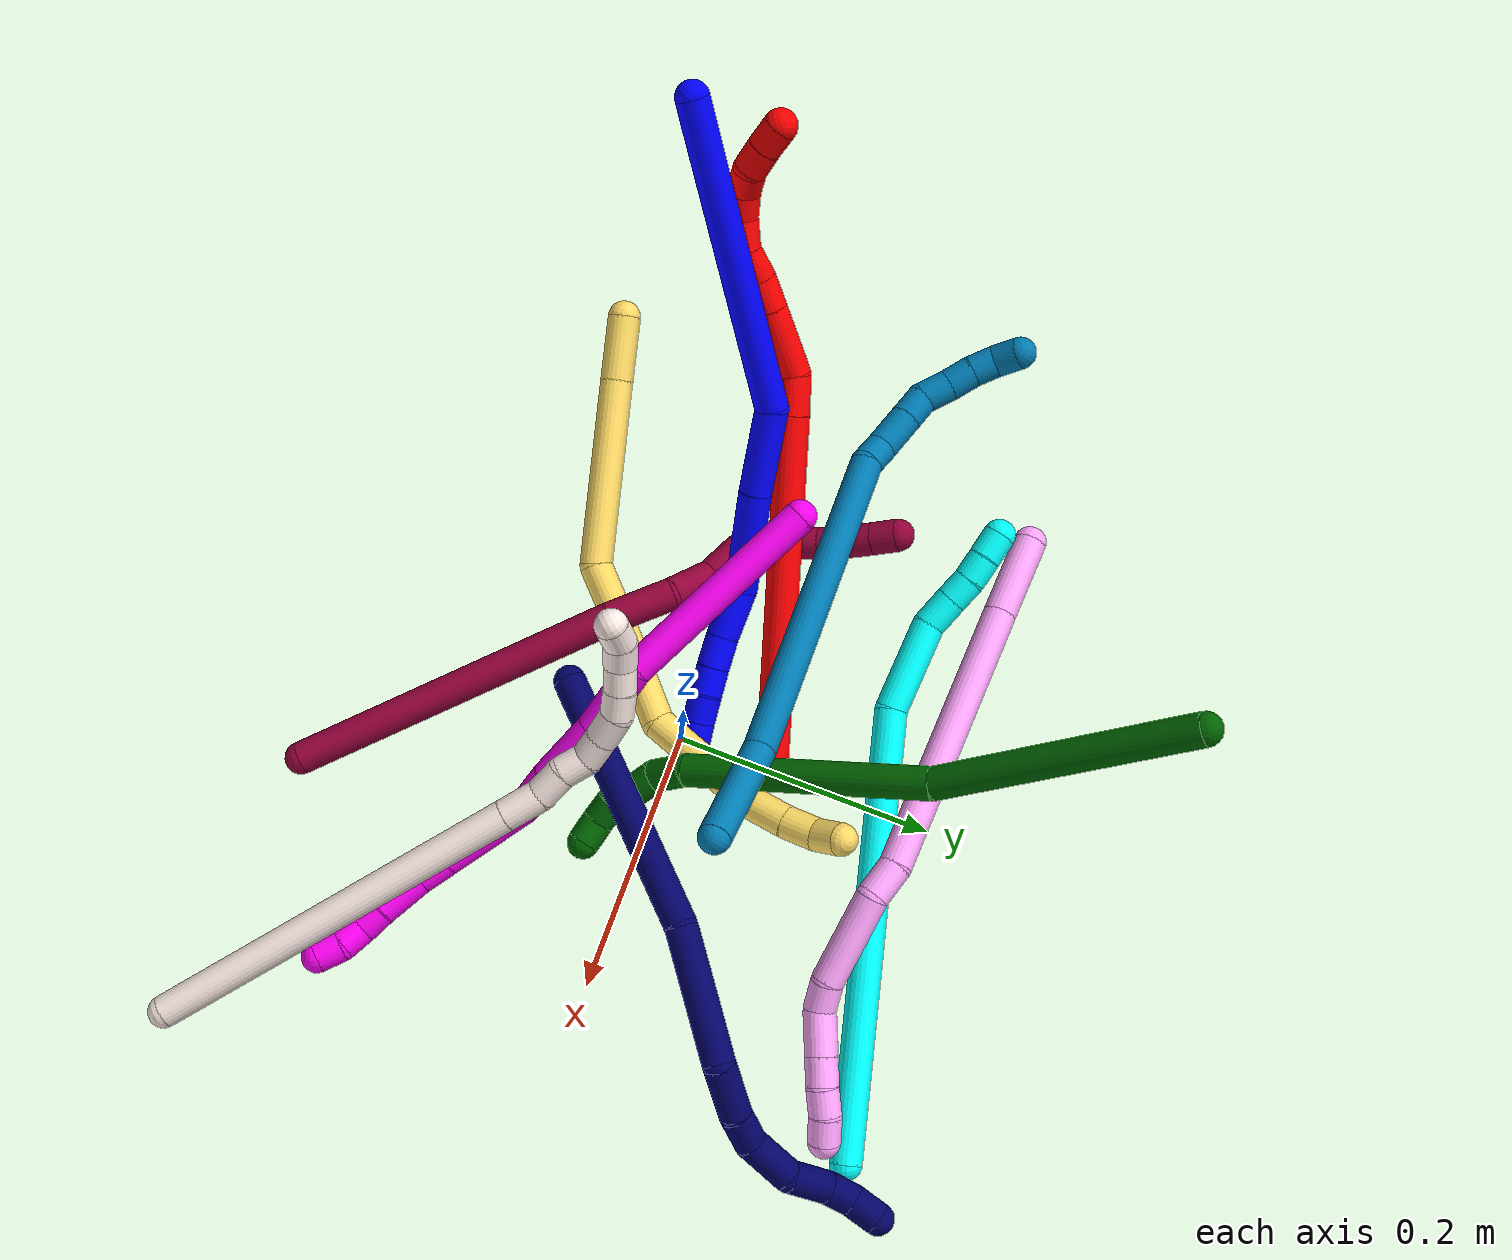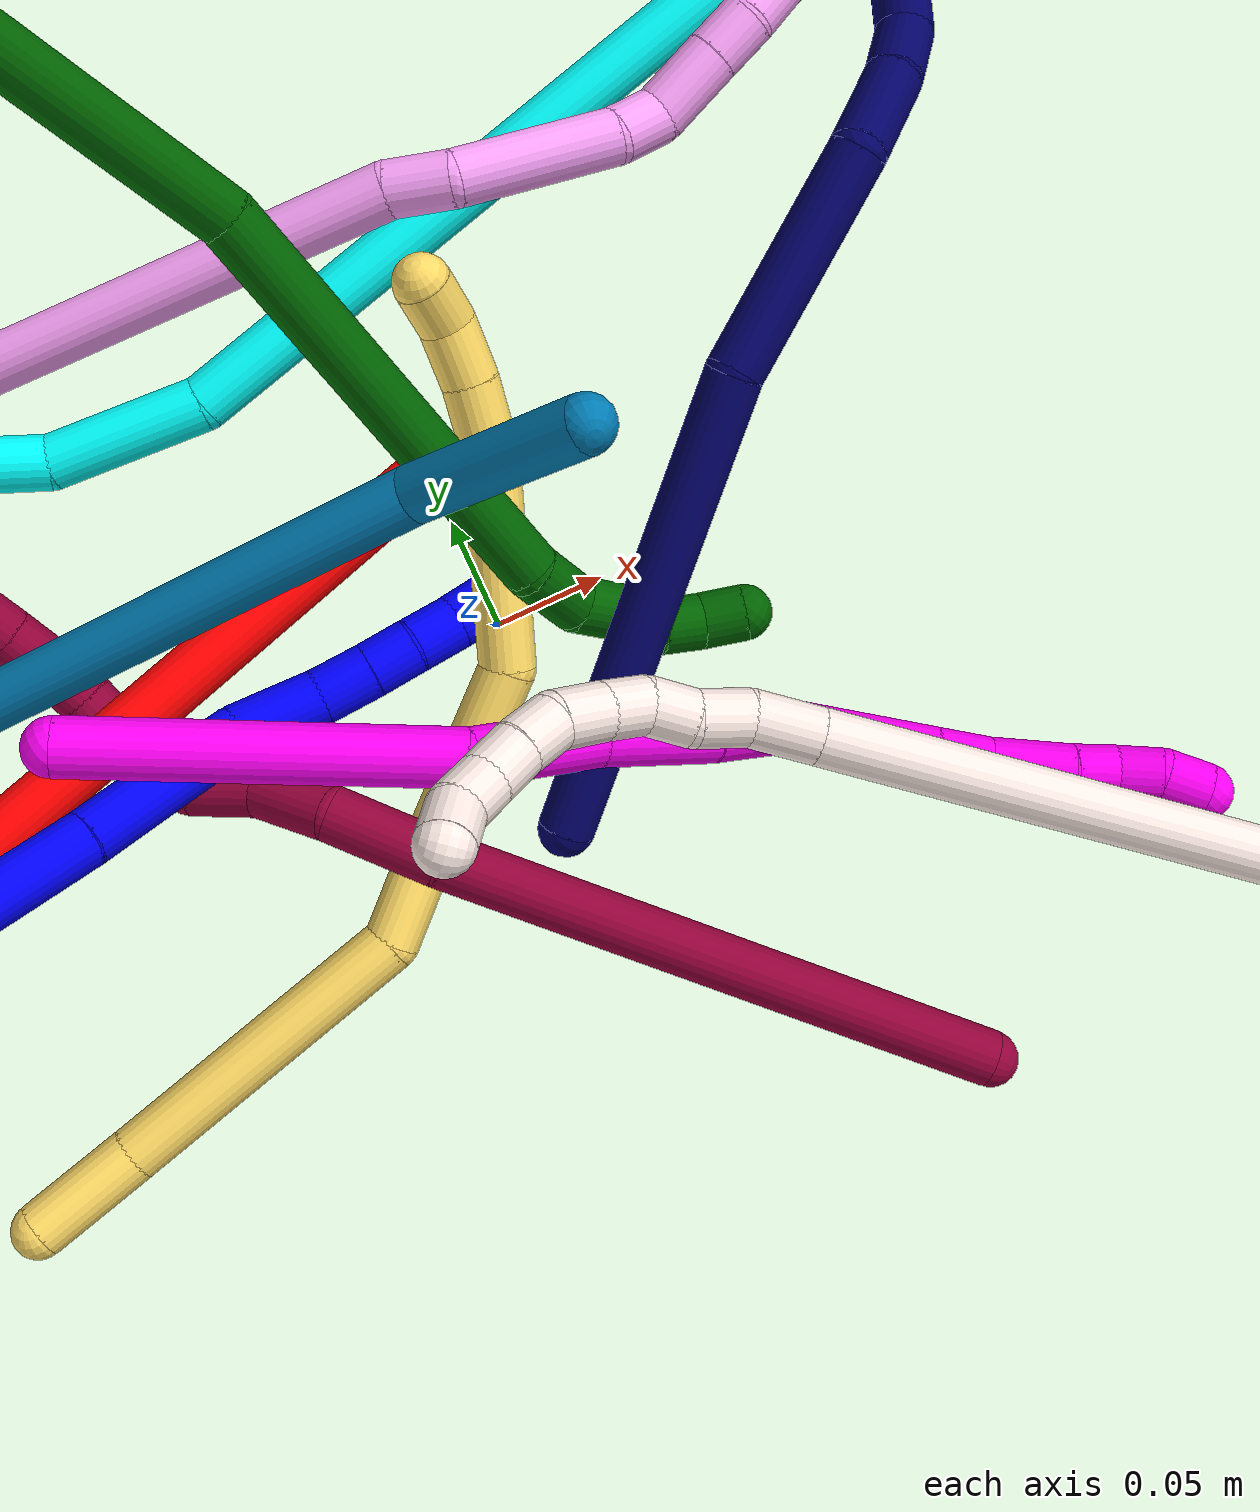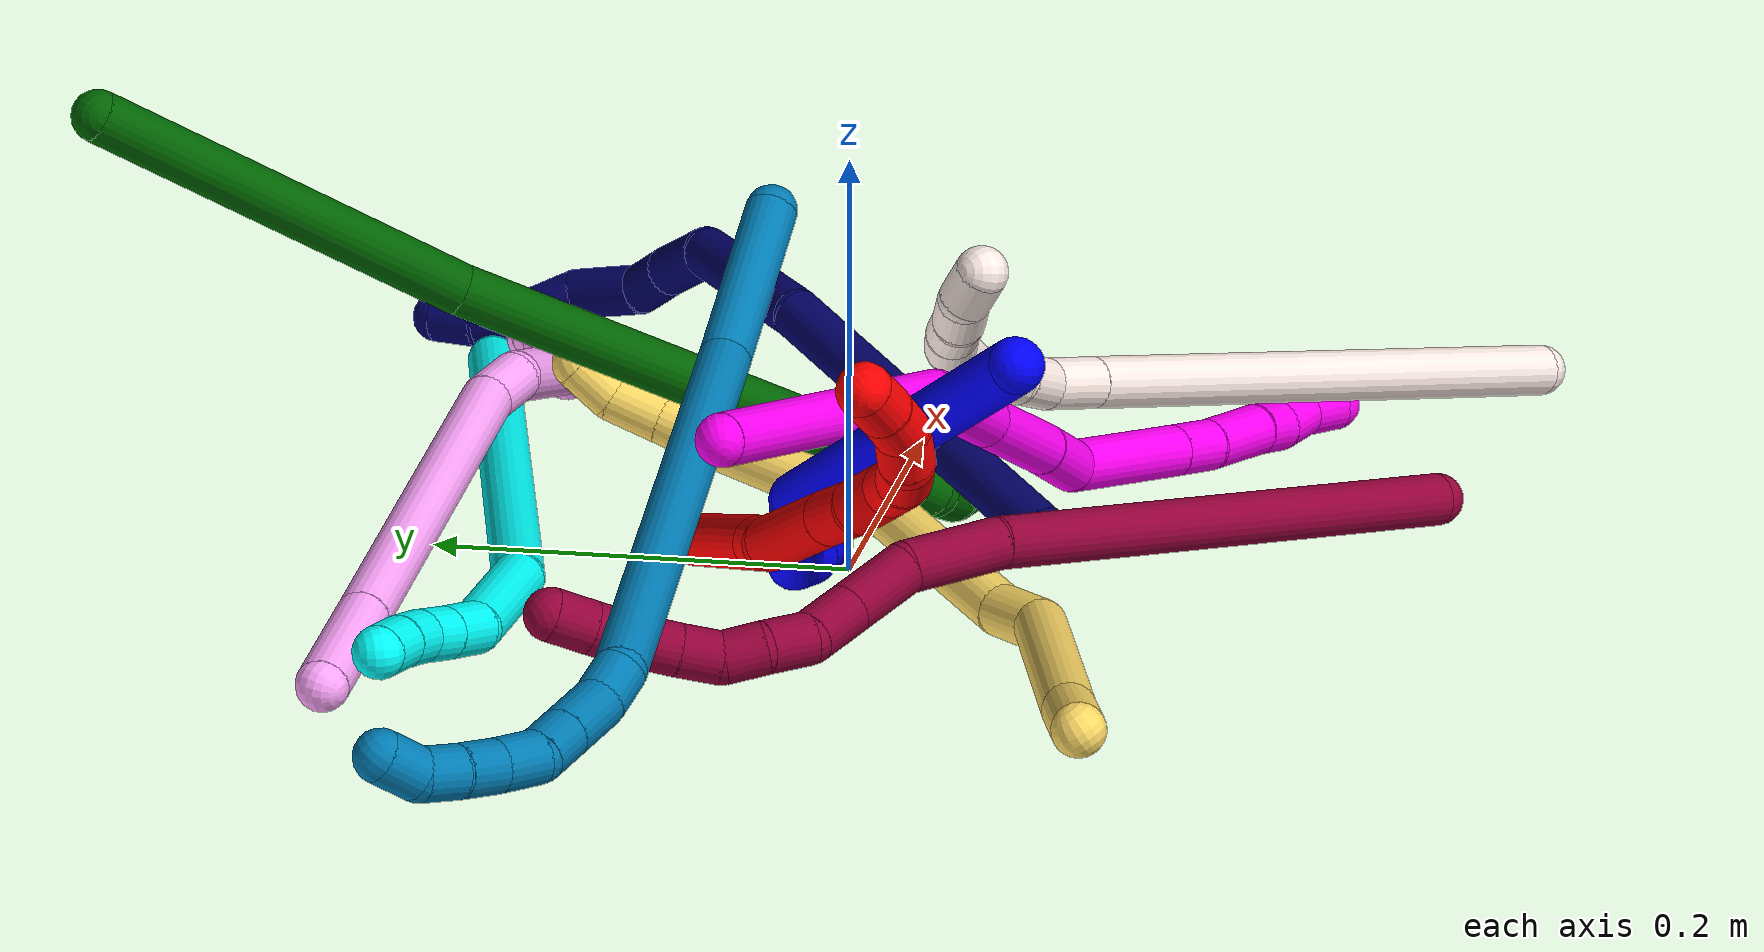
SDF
<sdf version="1.7">
 <world name="default">
  <plugin name="TubeGeneratorPlugin" filename="libtube_generator_plugin.so"/>
  <model name="photoneo_s_sensor">
   <static>1</static>
   <pose>0 0 2 1.57079 1.57079 3.14159</pose>
   <link name="link">
    <inertial><mass>0.1</mass></inertial>
    <sensor name="sensor" type="depth">
     <update_rate>30</update_rate>
     <camera>
      <horizontal_fov>1.22</horizontal_fov>
      <image><width>1920</width><height>1200</height><format>B8G8R8</format></image>
      <clip><near>0.1</near><far>4</far></clip>
      <depth_camera><output>points</output></depth_camera>
     </camera>
     <plugin name="camera_plugin" filename="libgazebo_ros_depth_camera.so">
      <baseline>0.2</baseline>
      <alwaysOn>1</alwaysOn>
      <updateRate>0.0</updateRate>
      <cameraName>camera_ir</cameraName>
      <imageTopicName>/camera/color/image_raw</imageTopicName>
      <cameraInfoTopicName>/camera/color/camera_info</cameraInfoTopicName>
      <depthImageTopicName>/camera/depth/image_raw</depthImageTopicName>
      <depthImageCameraInfoTopicName>/camera/depth/camera_info</depthImageCameraInfoTopicName>
      <pointCloudTopicName>/camera/depth/points</pointCloudTopicName>
      <frameName>fr_optical</frameName>
      <pointCloudCutoff>0.1</pointCloudCutoff>
      <pointCloudCutoffMax>2.0</pointCloudCutoffMax>
      <distortionK1>0</distortionK1>
      <distortionK2>0</distortionK2>
      <distortionK3>0</distortionK3>
      <distortionT1>0</distortionT1>
      <distortionT2>0</distortionT2>
      <CxPrime>0</CxPrime>
      <Cx>0</Cx>
      <Cy>0</Cy>
      <focalLength>0</focalLength>
      <hackBaseline>0</hackBaseline>
     </plugin>
    </sensor>
   </link>
  </model>
  <gravity>0 0 -9.8</gravity>
  <magnetic_field>6e-06 2.3e-05 -4.2e-05</magnetic_field>
  <atmosphere type="adiabatic"/>
  <physics name="default_physics" default="0" type="ode">
   <max_step_size>0.003</max_step_size>
   <real_time_factor>1</real_time_factor>
   <real_time_update_rate>1000</real_time_update_rate>
   <max_contacts>10000</max_contacts>
   <ode>
    <solver>
     <type>quick</type>
     <iters>100</iters>
     <sor>1.3</sor>
     <use_dynamic_moi_rescaling>0</use_dynamic_moi_rescaling>
    </solver>
    <constraints>
     <contact_max_correcting_vel>0</contact_max_correcting_vel>
     <contact_surface_layer>0.001</contact_surface_layer>
     <cfm>0</cfm>
     <erp>0.2</erp>
    </constraints>
   </ode>
  </physics>
  <scene><ambient>0.4 0.4 0.4 1</ambient><background>0.7 0.7 0.7 1</background><shadows>0</shadows></scene>
  <audio><device>default</device></audio>
  <spherical_coordinates>
   <surface_model>EARTH_WGS84</surface_model>
   <latitude_deg>0</latitude_deg>
   <longitude_deg>0</longitude_deg>
   <elevation>0</elevation>
   <heading_deg>0</heading_deg>
  </spherical_coordinates>
  <model name="bin">
   <static>1</static>
   <link name="bottom">
    <collision name="collision-bottom">
     <pose>0 0 -0.01 0 -0 0</pose>
     <geometry><box><size>0.8 0.6 0.02</size></box></geometry>
     <surface>
      <friction><ode><mu>100</mu><mu2>100</mu2></ode></friction>
      <contact><collide_bitmask>65535</collide_bitmask></contact>
     </surface>
    </collision>
   </link>
   <link name="west_wall">
    <collision name="collision-west_wall">
     <pose>-0.41 0 0.1 0 -0 0</pose>
     <geometry><box><size>0.02 0.6 0.2</size></box></geometry>
     <surface>
      <friction><ode><mu>100</mu><mu2>100</mu2></ode></friction>
      <contact><collide_bitmask>65535</collide_bitmask></contact>
     </surface>
    </collision>
   </link>
   <link name="east_wall">
    <collision name="collision-east_wall">
     <pose>0.41 0 0.1 0 -0 0</pose>
     <geometry><box><size>0.02 0.6 0.2</size></box></geometry>
     <surface>
      <friction><ode><mu>100</mu><mu2>100</mu2></ode></friction>
      <contact><collide_bitmask>65535</collide_bitmask></contact>
     </surface>
    </collision>
   </link>
   <link name="south_wall">
    <collision name="collision-south_wall">
     <pose>0 -0.31 0.1 0 -0 0</pose>
     <geometry><box><size>0.8 0.02 0.2</size></box></geometry>
     <surface>
      <friction><ode><mu>100</mu><mu2>100</mu2></ode></friction>
      <contact><collide_bitmask>65535</collide_bitmask></contact>
     </surface>
    </collision>
   </link>
   <link name="north_wall">
    <collision name="collision-north_wall">
     <pose>0 0.31 0.1 0 -0 0</pose>
     <geometry><box><size>0.8 0.02 0.2</size></box></geometry>
     <surface>
      <friction><ode><mu>100</mu><mu2>100</mu2></ode></friction>
      <contact><collide_bitmask>65535</collide_bitmask></contact>
     </surface>
    </collision>
   </link>
  </model>
  <model name="1">
   <static>0</static>
   <link name="1">
    <collision name="collision-cylinder-e_1_1_4">
     <pose>0.096894 0.03829 -0.051251 -2.49995 0.987248 -2.03507</pose>
     <geometry><cylinder><radius>0.0125</radius><length>0.232217</length></cylinder></geometry>
     <surface>
      <friction><ode><mu>1.16</mu><mu2>1.16</mu2><slip1>0</slip1><slip2>0</slip2></ode></friction>
      <contact><ode><kp>1e+06</kp><kd>1</kd><max_vel>0</max_vel><min_depth>0.001</min_depth></ode></contact>
     </surface>
    </collision>
    <visual name="visual-cylinder-e_1_1_4">
     <pose>0.096894 0.03829 -0.051251 -2.49995 0.987248 -2.03507</pose>
     <geometry><cylinder><radius>0.0125</radius><length>0.232217</length></cylinder></geometry>
     <material><ambient>0 0 1 1</ambient></material>
    </visual>
    <collision name="collision-cylinder-e_2_4_5">
     <pose>0.211817 0.086426 -0.127335 -2.7641 0.593663 -2.02508</pose>
     <geometry><cylinder><radius>0.0125</radius><length>0.064456</length></cylinder></geometry>
     <surface>
      <friction><ode><mu>1.16</mu><mu2>1.16</mu2><slip1>0</slip1><slip2>0</slip2></ode></friction>
      <contact><ode><kp>1e+06</kp><kd>1</kd><max_vel>0</max_vel><min_depth>0.001</min_depth></ode></contact>
     </surface>
    </collision>
    <visual name="visual-cylinder-e_2_4_5">
     <pose>0.211817 0.086426 -0.127335 -2.7641 0.593663 -2.02508</pose>
     <geometry><cylinder><radius>0.0125</radius><length>0.064456</length></cylinder></geometry>
     <material><ambient>0 0 1 1</ambient></material>
    </visual>
    <collision name="collision-cylinder-e_3_5_6">
     <pose>0.252804 0.109908 -0.180625 -2.69477 0.628975 -1.92217</pose>
     <geometry><cylinder><radius>0.0125</radius><length>0.078048</length></cylinder></geometry>
     <surface>
      <friction><ode><mu>1.16</mu><mu2>1.16</mu2><slip1>0</slip1><slip2>0</slip2></ode></friction>
      <contact><ode><kp>1e+06</kp><kd>1</kd><max_vel>0</max_vel><min_depth>0.001</min_depth></ode></contact>
     </surface>
    </collision>
    <visual name="visual-cylinder-e_3_5_6">
     <pose>0.252804 0.109908 -0.180625 -2.69477 0.628975 -1.92217</pose>
     <geometry><cylinder><radius>0.0125</radius><length>0.078048</length></cylinder></geometry>
     <material><ambient>0 0 1 1</ambient></material>
    </visual>
    <collision name="collision-cylinder-e_4_6_7">
     <pose>0.28385 0.125041 -0.2265 -3.05581 0.433335 -2.75647</pose>
     <geometry><cylinder><radius>0.0125</radius><length>0.038522</length></cylinder></geometry>
     <surface>
      <friction><ode><mu>1.16</mu><mu2>1.16</mu2><slip1>0</slip1><slip2>0</slip2></ode></friction>
      <contact><ode><kp>1e+06</kp><kd>1</kd><max_vel>0</max_vel><min_depth>0.001</min_depth></ode></contact>
     </surface>
    </collision>
    <visual name="visual-cylinder-e_4_6_7">
     <pose>0.28385 0.125041 -0.2265 -3.05581 0.433335 -2.75647</pose>
     <geometry><cylinder><radius>0.0125</radius><length>0.038522</length></cylinder></geometry>
     <material><ambient>0 0 1 1</ambient></material>
    </visual>
    <collision name="collision-cylinder-e_5_7_8">
     <pose>0.297772 0.126433 -0.254546 3.13168 0.501995 3.10292</pose>
     <geometry><cylinder><radius>0.0125</radius><length>0.024252</length></cylinder></geometry>
     <surface>
      <friction><ode><mu>1.16</mu><mu2>1.16</mu2><slip1>0</slip1><slip2>0</slip2></ode></friction>
      <contact><ode><kp>1e+06</kp><kd>1</kd><max_vel>0</max_vel><min_depth>0.001</min_depth></ode></contact>
     </surface>
    </collision>
    <visual name="visual-cylinder-e_5_7_8">
     <pose>0.297772 0.126433 -0.254546 3.13168 0.501995 3.10292</pose>
     <geometry><cylinder><radius>0.0125</radius><length>0.024252</length></cylinder></geometry>
     <material><ambient>0 0 1 1</ambient></material>
    </visual>
    <collision name="collision-cylinder-e_6_8_9">
     <pose>0.309044 0.126449 -0.274218 -3.12821 0.541305 -3.09336</pose>
     <geometry><cylinder><radius>0.0125</radius><length>0.021105</length></cylinder></geometry>
     <surface>
      <friction><ode><mu>1.16</mu><mu2>1.16</mu2><slip1>0</slip1><slip2>0</slip2></ode></friction>
      <contact><ode><kp>1e+06</kp><kd>1</kd><max_vel>0</max_vel><min_depth>0.001</min_depth></ode></contact>
     </surface>
    </collision>
    <visual name="visual-cylinder-e_6_8_9">
     <pose>0.309044 0.126449 -0.274218 -3.12821 0.541305 -3.09336</pose>
     <geometry><cylinder><radius>0.0125</radius><length>0.021105</length></cylinder></geometry>
     <material><ambient>0 0 1 1</ambient></material>
    </visual>
    <collision name="collision-cylinder-e_7_9_10">
     <pose>0.319929 0.12815 -0.292184 -2.96634 0.541311 -2.52832</pose>
     <geometry><cylinder><radius>0.0125</radius><length>0.021145</length></cylinder></geometry>
     <surface>
      <friction><ode><mu>1.16</mu><mu2>1.16</mu2><slip1>0</slip1><slip2>0</slip2></ode></friction>
      <contact><ode><kp>1e+06</kp><kd>1</kd><max_vel>0</max_vel><min_depth>0.001</min_depth></ode></contact>
     </surface>
    </collision>
    <visual name="visual-cylinder-e_7_9_10">
     <pose>0.319929 0.12815 -0.292184 -2.96634 0.541311 -2.52832</pose>
     <geometry><cylinder><radius>0.0125</radius><length>0.021145</length></cylinder></geometry>
     <material><ambient>0 0 1 1</ambient></material>
    </visual>
    <collision name="collision-cylinder-e_8_10_2">
     <pose>0.330995 0.130854 -0.309456 -3.00775 0.588131 -2.70599</pose>
     <geometry><cylinder><radius>0.0125</radius><length>0.020255</length></cylinder></geometry>
     <surface>
      <friction><ode><mu>1.16</mu><mu2>1.16</mu2><slip1>0</slip1><slip2>0</slip2></ode></friction>
      <contact><ode><kp>1e+06</kp><kd>1</kd><max_vel>0</max_vel><min_depth>0.001</min_depth></ode></contact>
     </surface>
    </collision>
    <visual name="visual-cylinder-e_8_10_2">
     <pose>0.330995 0.130854 -0.309456 -3.00775 0.588131 -2.70599</pose>
     <geometry><cylinder><radius>0.0125</radius><length>0.020255</length></cylinder></geometry>
     <material><ambient>0 0 1 1</ambient></material>
    </visual>
    <collision name="collision-sphere-2">
     <pose>0.336614 0.131978 -0.317806 0 -0 0</pose>
     <geometry><sphere><radius>0.0125</radius></sphere></geometry>
     <surface>
      <friction><ode><mu>1.16</mu><mu2>1.16</mu2><slip1>0</slip1><slip2>0</slip2></ode></friction>
      <contact><ode><kp>1e+06</kp><kd>1</kd><max_vel>0</max_vel><min_depth>0.001</min_depth></ode></contact>
     </surface>
    </collision>
    <visual name="visual-sphere-2">
     <pose>0.336614 0.131978 -0.317806 0 -0 0</pose>
     <geometry><sphere><radius>0.0125</radius></sphere></geometry>
     <material><ambient>0 0 1 1</ambient></material>
    </visual>
    <collision name="collision-sphere-10">
     <pose>0.325376 0.129729 -0.301106 0 -0 0</pose>
     <geometry><sphere><radius>0.0125</radius></sphere></geometry>
     <surface>
      <friction><ode><mu>1.16</mu><mu2>1.16</mu2><slip1>0</slip1><slip2>0</slip2></ode></friction>
      <contact><ode><kp>1e+06</kp><kd>1</kd><max_vel>0</max_vel><min_depth>0.001</min_depth></ode></contact>
     </surface>
    </collision>
    <visual name="visual-sphere-10">
     <pose>0.325376 0.129729 -0.301106 0 -0 0</pose>
     <geometry><sphere><radius>0.0125</radius></sphere></geometry>
     <material><ambient>0 0 1 1</ambient></material>
    </visual>
    <collision name="collision-sphere-9">
     <pose>0.314481 0.12657 -0.283262 0 -0 0</pose>
     <geometry><sphere><radius>0.0125</radius></sphere></geometry>
     <surface>
      <friction><ode><mu>1.16</mu><mu2>1.16</mu2><slip1>0</slip1><slip2>0</slip2></ode></friction>
      <contact><ode><kp>1e+06</kp><kd>1</kd><max_vel>0</max_vel><min_depth>0.001</min_depth></ode></contact>
     </surface>
    </collision>
    <visual name="visual-sphere-9">
     <pose>0.314481 0.12657 -0.283262 0 -0 0</pose>
     <geometry><sphere><radius>0.0125</radius></sphere></geometry>
     <material><ambient>0 0 1 1</ambient></material>
    </visual>
    <collision name="collision-sphere-4">
     <pose>0.193788 0.076579 -0.102502 0 -0 0</pose>
     <geometry><sphere><radius>0.0125</radius></sphere></geometry>
     <surface>
      <friction><ode><mu>1.16</mu><mu2>1.16</mu2><slip1>0</slip1><slip2>0</slip2></ode></friction>
      <contact><ode><kp>1e+06</kp><kd>1</kd><max_vel>0</max_vel><min_depth>0.001</min_depth></ode></contact>
     </surface>
    </collision>
    <visual name="visual-sphere-4">
     <pose>0.193788 0.076579 -0.102502 0 -0 0</pose>
     <geometry><sphere><radius>0.0125</radius></sphere></geometry>
     <material><ambient>0 0 1 1</ambient></material>
    </visual>
    <collision name="collision-sphere-1">
     <geometry><sphere><radius>0.0125</radius></sphere></geometry>
     <surface>
      <friction><ode><mu>1.16</mu><mu2>1.16</mu2><slip1>0</slip1><slip2>0</slip2></ode></friction>
      <contact><ode><kp>1e+06</kp><kd>1</kd><max_vel>0</max_vel><min_depth>0.001</min_depth></ode></contact>
     </surface>
    </collision>
    <visual name="visual-sphere-1">
     <geometry><sphere><radius>0.0125</radius></sphere></geometry>
     <material><ambient>0 0 1 1</ambient></material>
    </visual>
    <collision name="collision-sphere-8">
     <pose>0.303607 0.126328 -0.265175 0 -0 0</pose>
     <geometry><sphere><radius>0.0125</radius></sphere></geometry>
     <surface>
      <friction><ode><mu>1.16</mu><mu2>1.16</mu2><slip1>0</slip1><slip2>0</slip2></ode></friction>
      <contact><ode><kp>1e+06</kp><kd>1</kd><max_vel>0</max_vel><min_depth>0.001</min_depth></ode></contact>
     </surface>
    </collision>
    <visual name="visual-sphere-8">
     <pose>0.303607 0.126328 -0.265175 0 -0 0</pose>
     <geometry><sphere><radius>0.0125</radius></sphere></geometry>
     <material><ambient>0 0 1 1</ambient></material>
    </visual>
    <collision name="collision-sphere-5">
     <pose>0.229845 0.096272 -0.152168 0 -0 0</pose>
     <geometry><sphere><radius>0.0125</radius></sphere></geometry>
     <surface>
      <friction><ode><mu>1.16</mu><mu2>1.16</mu2><slip1>0</slip1><slip2>0</slip2></ode></friction>
      <contact><ode><kp>1e+06</kp><kd>1</kd><max_vel>0</max_vel><min_depth>0.001</min_depth></ode></contact>
     </surface>
    </collision>
    <visual name="visual-sphere-5">
     <pose>0.229845 0.096272 -0.152168 0 -0 0</pose>
     <geometry><sphere><radius>0.0125</radius></sphere></geometry>
     <material><ambient>0 0 1 1</ambient></material>
    </visual>
    <collision name="collision-sphere-6">
     <pose>0.275762 0.123543 -0.209083 0 -0 0</pose>
     <geometry><sphere><radius>0.0125</radius></sphere></geometry>
     <surface>
      <friction><ode><mu>1.16</mu><mu2>1.16</mu2><slip1>0</slip1><slip2>0</slip2></ode></friction>
      <contact><ode><kp>1e+06</kp><kd>1</kd><max_vel>0</max_vel><min_depth>0.001</min_depth></ode></contact>
     </surface>
    </collision>
    <visual name="visual-sphere-6">
     <pose>0.275762 0.123543 -0.209083 0 -0 0</pose>
     <geometry><sphere><radius>0.0125</radius></sphere></geometry>
     <material><ambient>0 0 1 1</ambient></material>
    </visual>
    <collision name="collision-sphere-7">
     <pose>0.291937 0.126539 -0.243916 0 -0 0</pose>
     <geometry><sphere><radius>0.0125</radius></sphere></geometry>
     <surface>
      <friction><ode><mu>1.16</mu><mu2>1.16</mu2><slip1>0</slip1><slip2>0</slip2></ode></friction>
      <contact><ode><kp>1e+06</kp><kd>1</kd><max_vel>0</max_vel><min_depth>0.001</min_depth></ode></contact>
     </surface>
    </collision>
    <visual name="visual-sphere-7">
     <pose>0.291937 0.126539 -0.243916 0 -0 0</pose>
     <geometry><sphere><radius>0.0125</radius></sphere></geometry>
     <material><ambient>0 0 1 1</ambient></material>
    </visual>
    <inertial>
     <pose>0.188063 0.077904 -0.134677 0 -0 0</pose>
     <mass>0.5</mass>
     <inertia>
      <ixx>-0.000838</ixx>
      <ixy>0</ixy>
      <ixz>0</ixz>
      <iyy>0.000336</iyy>
      <iyz>0</iyz>
      <izz>-0.001319</izz>
     </inertia>
    </inertial>
   </link>
   <pose>-0.396332 -0.143791 0.231372 -1.45106 0.158123 1.14605</pose>
  </model>
  <model name="2">
   <static>0</static>
   <link name="2">
    <collision name="collision-cylinder-e_1_1_4">
     <pose>-0.053926 -0.037985 0.115306 0.318231 -0.418017 -0.068048</pose>
     <geometry><cylinder><radius>0.0125</radius><length>0.265679</length></cylinder></geometry>
     <surface>
      <friction><ode><mu>1.16</mu><mu2>1.16</mu2><slip1>0</slip1><slip2>0</slip2></ode></friction>
      <contact><ode><kp>1e+06</kp><kd>1</kd><max_vel>0</max_vel><min_depth>0.001</min_depth></ode></contact>
     </surface>
    </collision>
    <visual name="visual-cylinder-e_1_1_4">
     <pose>-0.053926 -0.037985 0.115306 0.318231 -0.418017 -0.068048</pose>
     <geometry><cylinder><radius>0.0125</radius><length>0.265679</length></cylinder></geometry>
     <material><ambient>1 0 0 1</ambient></material>
    </visual>
    <collision name="collision-cylinder-e_2_4_5">
     <pose>-0.113852 -0.079916 0.243624 0.294497 -0.415581 -0.062522</pose>
     <geometry><cylinder><radius>0.0125</radius><length>0.029725</length></cylinder></geometry>
     <surface>
      <friction><ode><mu>1.16</mu><mu2>1.16</mu2><slip1>0</slip1><slip2>0</slip2></ode></friction>
      <contact><ode><kp>1e+06</kp><kd>1</kd><max_vel>0</max_vel><min_depth>0.001</min_depth></ode></contact>
     </surface>
    </collision>
    <visual name="visual-cylinder-e_2_4_5">
     <pose>-0.113852 -0.079916 0.243624 0.294497 -0.415581 -0.062522</pose>
     <geometry><cylinder><radius>0.0125</radius><length>0.029725</length></cylinder></geometry>
     <material><ambient>1 0 0 1</ambient></material>
    </visual>
    <collision name="collision-cylinder-e_3_5_6">
     <pose>-0.134971 -0.080459 0.27771 -0.160135 -0.616204 0.051059</pose>
     <geometry><cylinder><radius>0.0125</radius><length>0.052317</length></cylinder></geometry>
     <surface>
      <friction><ode><mu>1.16</mu><mu2>1.16</mu2><slip1>0</slip1><slip2>0</slip2></ode></friction>
      <contact><ode><kp>1e+06</kp><kd>1</kd><max_vel>0</max_vel><min_depth>0.001</min_depth></ode></contact>
     </surface>
    </collision>
    <visual name="visual-cylinder-e_3_5_6">
     <pose>-0.134971 -0.080459 0.27771 -0.160135 -0.616204 0.051059</pose>
     <geometry><cylinder><radius>0.0125</radius><length>0.052317</length></cylinder></geometry>
     <material><ambient>1 0 0 1</ambient></material>
    </visual>
    <collision name="collision-cylinder-e_4_6_7">
     <pose>-0.15673 -0.075455 0.308593 -0.161731 -0.589112 0.049163</pose>
     <geometry><cylinder><radius>0.0125</radius><length>0.023907</length></cylinder></geometry>
     <surface>
      <friction><ode><mu>1.16</mu><mu2>1.16</mu2><slip1>0</slip1><slip2>0</slip2></ode></friction>
      <contact><ode><kp>1e+06</kp><kd>1</kd><max_vel>0</max_vel><min_depth>0.001</min_depth></ode></contact>
     </surface>
    </collision>
    <visual name="visual-cylinder-e_4_6_7">
     <pose>-0.15673 -0.075455 0.308593 -0.161731 -0.589112 0.049163</pose>
     <geometry><cylinder><radius>0.0125</radius><length>0.023907</length></cylinder></geometry>
     <material><ambient>1 0 0 1</ambient></material>
    </visual>
    <collision name="collision-cylinder-e_5_7_8">
     <pose>-0.171203 -0.070571 0.327071 -0.362097 -0.701468 0.133744</pose>
     <geometry><cylinder><radius>0.0125</radius><length>0.024271</length></cylinder></geometry>
     <surface>
      <friction><ode><mu>1.16</mu><mu2>1.16</mu2><slip1>0</slip1><slip2>0</slip2></ode></friction>
      <contact><ode><kp>1e+06</kp><kd>1</kd><max_vel>0</max_vel><min_depth>0.001</min_depth></ode></contact>
     </surface>
    </collision>
    <visual name="visual-cylinder-e_5_7_8">
     <pose>-0.171203 -0.070571 0.327071 -0.362097 -0.701468 0.133744</pose>
     <geometry><cylinder><radius>0.0125</radius><length>0.024271</length></cylinder></geometry>
     <material><ambient>1 0 0 1</ambient></material>
    </visual>
    <collision name="collision-cylinder-e_6_8_9">
     <pose>-0.185494 -0.068885 0.345581 0.160946 -0.574885 -0.047674</pose>
     <geometry><cylinder><radius>0.0125</radius><length>0.023758</length></cylinder></geometry>
     <surface>
      <friction><ode><mu>1.16</mu><mu2>1.16</mu2><slip1>0</slip1><slip2>0</slip2></ode></friction>
      <contact><ode><kp>1e+06</kp><kd>1</kd><max_vel>0</max_vel><min_depth>0.001</min_depth></ode></contact>
     </surface>
    </collision>
    <visual name="visual-cylinder-e_6_8_9">
     <pose>-0.185494 -0.068885 0.345581 0.160946 -0.574885 -0.047674</pose>
     <geometry><cylinder><radius>0.0125</radius><length>0.023758</length></cylinder></geometry>
     <material><ambient>1 0 0 1</ambient></material>
    </visual>
    <collision name="collision-cylinder-e_7_9_10">
     <pose>-0.199145 -0.073306 0.361899 0.411063 -0.794172 -0.17441</pose>
     <geometry><cylinder><radius>0.0125</radius><length>0.020165</length></cylinder></geometry>
     <surface>
      <friction><ode><mu>1.16</mu><mu2>1.16</mu2><slip1>0</slip1><slip2>0</slip2></ode></friction>
      <contact><ode><kp>1e+06</kp><kd>1</kd><max_vel>0</max_vel><min_depth>0.001</min_depth></ode></contact>
     </surface>
    </collision>
    <visual name="visual-cylinder-e_7_9_10">
     <pose>-0.199145 -0.073306 0.361899 0.411063 -0.794172 -0.17441</pose>
     <geometry><cylinder><radius>0.0125</radius><length>0.020165</length></cylinder></geometry>
     <material><ambient>1 0 0 1</ambient></material>
    </visual>
    <collision name="collision-cylinder-e_8_10_11">
     <pose>-0.215204 -0.079478 0.371568 0.809365 -1.09002 -0.508127</pose>
     <geometry><cylinder><radius>0.0125</radius><length>0.020003</length></cylinder></geometry>
     <surface>
      <friction><ode><mu>1.16</mu><mu2>1.16</mu2><slip1>0</slip1><slip2>0</slip2></ode></friction>
      <contact><ode><kp>1e+06</kp><kd>1</kd><max_vel>0</max_vel><min_depth>0.001</min_depth></ode></contact>
     </surface>
    </collision>
    <visual name="visual-cylinder-e_8_10_11">
     <pose>-0.215204 -0.079478 0.371568 0.809365 -1.09002 -0.508127</pose>
     <geometry><cylinder><radius>0.0125</radius><length>0.020003</length></cylinder></geometry>
     <material><ambient>1 0 0 1</ambient></material>
    </visual>
    <collision name="collision-cylinder-e_9_11_12">
     <pose>-0.230961 -0.089163 0.378314 1.0597 -0.758844 -0.458872</pose>
     <geometry><cylinder><radius>0.0125</radius><length>0.020025</length></cylinder></geometry>
     <surface>
      <friction><ode><mu>1.16</mu><mu2>1.16</mu2><slip1>0</slip1><slip2>0</slip2></ode></friction>
      <contact><ode><kp>1e+06</kp><kd>1</kd><max_vel>0</max_vel><min_depth>0.001</min_depth></ode></contact>
     </surface>
    </collision>
    <visual name="visual-cylinder-e_9_11_12">
     <pose>-0.230961 -0.089163 0.378314 1.0597 -0.758844 -0.458872</pose>
     <geometry><cylinder><radius>0.0125</radius><length>0.020025</length></cylinder></geometry>
     <material><ambient>1 0 0 1</ambient></material>
    </visual>
    <collision name="collision-cylinder-e_10_12_2">
     <pose>-0.244588 -0.102273 0.385069 1.12929 -0.732405 -0.476615</pose>
     <geometry><cylinder><radius>0.0125</radius><length>0.02015</length></cylinder></geometry>
     <surface>
      <friction><ode><mu>1.16</mu><mu2>1.16</mu2><slip1>0</slip1><slip2>0</slip2></ode></friction>
      <contact><ode><kp>1e+06</kp><kd>1</kd><max_vel>0</max_vel><min_depth>0.001</min_depth></ode></contact>
     </surface>
    </collision>
    <visual name="visual-cylinder-e_10_12_2">
     <pose>-0.244588 -0.102273 0.385069 1.12929 -0.732405 -0.476615</pose>
     <geometry><cylinder><radius>0.0125</radius><length>0.02015</length></cylinder></geometry>
     <material><ambient>1 0 0 1</ambient></material>
    </visual>
    <collision name="collision-sphere-2">
     <pose>-0.251325 -0.109047 0.38827 0 -0 0</pose>
     <geometry><sphere><radius>0.0125</radius></sphere></geometry>
     <surface>
      <friction><ode><mu>1.16</mu><mu2>1.16</mu2><slip1>0</slip1><slip2>0</slip2></ode></friction>
      <contact><ode><kp>1e+06</kp><kd>1</kd><max_vel>0</max_vel><min_depth>0.001</min_depth></ode></contact>
     </surface>
    </collision>
    <visual name="visual-sphere-2">
     <pose>-0.251325 -0.109047 0.38827 0 -0 0</pose>
     <geometry><sphere><radius>0.0125</radius></sphere></geometry>
     <material><ambient>1 0 0 1</ambient></material>
    </visual>
    <collision name="collision-sphere-12">
     <pose>-0.237851 -0.0955 0.381867 0 -0 0</pose>
     <geometry><sphere><radius>0.0125</radius></sphere></geometry>
     <surface>
      <friction><ode><mu>1.16</mu><mu2>1.16</mu2><slip1>0</slip1><slip2>0</slip2></ode></friction>
      <contact><ode><kp>1e+06</kp><kd>1</kd><max_vel>0</max_vel><min_depth>0.001</min_depth></ode></contact>
     </surface>
    </collision>
    <visual name="visual-sphere-12">
     <pose>-0.237851 -0.0955 0.381867 0 -0 0</pose>
     <geometry><sphere><radius>0.0125</radius></sphere></geometry>
     <material><ambient>1 0 0 1</ambient></material>
    </visual>
    <collision name="collision-sphere-11">
     <pose>-0.224072 -0.082826 0.37476 0 -0 0</pose>
     <geometry><sphere><radius>0.0125</radius></sphere></geometry>
     <surface>
      <friction><ode><mu>1.16</mu><mu2>1.16</mu2><slip1>0</slip1><slip2>0</slip2></ode></friction>
      <contact><ode><kp>1e+06</kp><kd>1</kd><max_vel>0</max_vel><min_depth>0.001</min_depth></ode></contact>
     </surface>
    </collision>
    <visual name="visual-sphere-11">
     <pose>-0.224072 -0.082826 0.37476 0 -0 0</pose>
     <geometry><sphere><radius>0.0125</radius></sphere></geometry>
     <material><ambient>1 0 0 1</ambient></material>
    </visual>
    <collision name="collision-sphere-10">
     <pose>-0.206336 -0.07613 0.368377 0 -0 0</pose>
     <geometry><sphere><radius>0.0125</radius></sphere></geometry>
     <surface>
      <friction><ode><mu>1.16</mu><mu2>1.16</mu2><slip1>0</slip1><slip2>0</slip2></ode></friction>
      <contact><ode><kp>1e+06</kp><kd>1</kd><max_vel>0</max_vel><min_depth>0.001</min_depth></ode></contact>
     </surface>
    </collision>
    <visual name="visual-sphere-10">
     <pose>-0.206336 -0.07613 0.368377 0 -0 0</pose>
     <geometry><sphere><radius>0.0125</radius></sphere></geometry>
     <material><ambient>1 0 0 1</ambient></material>
    </visual>
    <collision name="collision-sphere-9">
     <pose>-0.191953 -0.070483 0.355421 0 -0 0</pose>
     <geometry><sphere><radius>0.0125</radius></sphere></geometry>
     <surface>
      <friction><ode><mu>1.16</mu><mu2>1.16</mu2><slip1>0</slip1><slip2>0</slip2></ode></friction>
      <contact><ode><kp>1e+06</kp><kd>1</kd><max_vel>0</max_vel><min_depth>0.001</min_depth></ode></contact>
     </surface>
    </collision>
    <visual name="visual-sphere-9">
     <pose>-0.191953 -0.070483 0.355421 0 -0 0</pose>
     <geometry><sphere><radius>0.0125</radius></sphere></geometry>
     <material><ambient>1 0 0 1</ambient></material>
    </visual>
    <collision name="collision-sphere-4">
     <pose>-0.107852 -0.07597 0.230612 0 -0 0</pose>
     <geometry><sphere><radius>0.0125</radius></sphere></geometry>
     <surface>
      <friction><ode><mu>1.16</mu><mu2>1.16</mu2><slip1>0</slip1><slip2>0</slip2></ode></friction>
      <contact><ode><kp>1e+06</kp><kd>1</kd><max_vel>0</max_vel><min_depth>0.001</min_depth></ode></contact>
     </surface>
    </collision>
    <visual name="visual-sphere-4">
     <pose>-0.107852 -0.07597 0.230612 0 -0 0</pose>
     <geometry><sphere><radius>0.0125</radius></sphere></geometry>
     <material><ambient>1 0 0 1</ambient></material>
    </visual>
    <collision name="collision-sphere-1">
     <geometry><sphere><radius>0.0125</radius></sphere></geometry>
     <surface>
      <friction><ode><mu>1.16</mu><mu2>1.16</mu2><slip1>0</slip1><slip2>0</slip2></ode></friction>
      <contact><ode><kp>1e+06</kp><kd>1</kd><max_vel>0</max_vel><min_depth>0.001</min_depth></ode></contact>
     </surface>
    </collision>
    <visual name="visual-sphere-1">
     <geometry><sphere><radius>0.0125</radius></sphere></geometry>
     <material><ambient>1 0 0 1</ambient></material>
    </visual>
    <collision name="collision-sphere-8">
     <pose>-0.179035 -0.067287 0.33574 0 -0 0</pose>
     <geometry><sphere><radius>0.0125</radius></sphere></geometry>
     <surface>
      <friction><ode><mu>1.16</mu><mu2>1.16</mu2><slip1>0</slip1><slip2>0</slip2></ode></friction>
      <contact><ode><kp>1e+06</kp><kd>1</kd><max_vel>0</max_vel><min_depth>0.001</min_depth></ode></contact>
     </surface>
    </collision>
    <visual name="visual-sphere-8">
     <pose>-0.179035 -0.067287 0.33574 0 -0 0</pose>
     <geometry><sphere><radius>0.0125</radius></sphere></geometry>
     <material><ambient>1 0 0 1</ambient></material>
    </visual>
    <collision name="collision-sphere-5">
     <pose>-0.119853 -0.083863 0.256636 0 -0 0</pose>
     <geometry><sphere><radius>0.0125</radius></sphere></geometry>
     <surface>
      <friction><ode><mu>1.16</mu><mu2>1.16</mu2><slip1>0</slip1><slip2>0</slip2></ode></friction>
      <contact><ode><kp>1e+06</kp><kd>1</kd><max_vel>0</max_vel><min_depth>0.001</min_depth></ode></contact>
     </surface>
    </collision>
    <visual name="visual-sphere-5">
     <pose>-0.119853 -0.083863 0.256636 0 -0 0</pose>
     <geometry><sphere><radius>0.0125</radius></sphere></geometry>
     <material><ambient>1 0 0 1</ambient></material>
    </visual>
    <collision name="collision-sphere-6">
     <pose>-0.150089 -0.077056 0.298784 0 -0 0</pose>
     <geometry><sphere><radius>0.0125</radius></sphere></geometry>
     <surface>
      <friction><ode><mu>1.16</mu><mu2>1.16</mu2><slip1>0</slip1><slip2>0</slip2></ode></friction>
      <contact><ode><kp>1e+06</kp><kd>1</kd><max_vel>0</max_vel><min_depth>0.001</min_depth></ode></contact>
     </surface>
    </collision>
    <visual name="visual-sphere-6">
     <pose>-0.150089 -0.077056 0.298784 0 -0 0</pose>
     <geometry><sphere><radius>0.0125</radius></sphere></geometry>
     <material><ambient>1 0 0 1</ambient></material>
    </visual>
    <collision name="collision-sphere-7">
     <pose>-0.163372 -0.073855 0.318402 0 -0 0</pose>
     <geometry><sphere><radius>0.0125</radius></sphere></geometry>
     <surface>
      <friction><ode><mu>1.16</mu><mu2>1.16</mu2><slip1>0</slip1><slip2>0</slip2></ode></friction>
      <contact><ode><kp>1e+06</kp><kd>1</kd><max_vel>0</max_vel><min_depth>0.001</min_depth></ode></contact>
     </surface>
    </collision>
    <visual name="visual-sphere-7">
     <pose>-0.163372 -0.073855 0.318402 0 -0 0</pose>
     <geometry><sphere><radius>0.0125</radius></sphere></geometry>
     <material><ambient>1 0 0 1</ambient></material>
    </visual>
    <inertial>
     <pose>-0.109911 -0.057489 0.211993 0 -0 0</pose>
     <mass>0.5</mass>
     <inertia>
      <ixx>0.001339</ixx>
      <ixy>0</ixy>
      <ixz>0</ixz>
      <iyy>0.001425</iyy>
      <iyz>0</iyz>
      <izz>0.001137</izz>
     </inertia>
    </inertial>
   </link>
   <pose>-0.004056 0.072539 0.011873 -2.78448 1.44117 0.956356</pose>
  </model>
  <model name="3">
   <static>0</static>
   <link name="3">
    <collision name="collision-cylinder-e_1_1_4">
     <pose>-0.143132 -0.087944 0.03049 1.23707 -0.994208 -0.736984</pose>
     <geometry><cylinder><radius>0.0125</radius><length>0.34147</length></cylinder></geometry>
     <surface>
      <friction><ode><mu>1.16</mu><mu2>1.16</mu2><slip1>0</slip1><slip2>0</slip2></ode></friction>
      <contact><ode><kp>1e+06</kp><kd>1</kd><max_vel>0</max_vel><min_depth>0.001</min_depth></ode></contact>
     </surface>
    </collision>
    <visual name="visual-cylinder-e_1_1_4">
     <pose>-0.143132 -0.087944 0.03049 1.23707 -0.994208 -0.736984</pose>
     <geometry><cylinder><radius>0.0125</radius><length>0.34147</length></cylinder></geometry>
     <material><ambient>0.003922 1 0.996078 1</ambient></material>
    </visual>
    <collision name="collision-cylinder-e_2_4_5">
     <pose>-0.313141 -0.192211 0.077874 0.768242 -0.852496 -0.363043</pose>
     <geometry><cylinder><radius>0.0125</radius><length>0.071393</length></cylinder></geometry>
     <surface>
      <friction><ode><mu>1.16</mu><mu2>1.16</mu2><slip1>0</slip1><slip2>0</slip2></ode></friction>
      <contact><ode><kp>1e+06</kp><kd>1</kd><max_vel>0</max_vel><min_depth>0.001</min_depth></ode></contact>
     </surface>
    </collision>
    <visual name="visual-cylinder-e_2_4_5">
     <pose>-0.313141 -0.192211 0.077874 0.768242 -0.852496 -0.363043</pose>
     <geometry><cylinder><radius>0.0125</radius><length>0.071393</length></cylinder></geometry>
     <material><ambient>0.003922 1 0.996078 1</ambient></material>
    </visual>
    <collision name="collision-cylinder-e_3_5_6">
     <pose>-0.346307 -0.215281 0.10392 0.635128 -0.505257 -0.169292</pose>
     <geometry><cylinder><radius>0.0125</radius><length>0.025986</length></cylinder></geometry>
     <surface>
      <friction><ode><mu>1.16</mu><mu2>1.16</mu2><slip1>0</slip1><slip2>0</slip2></ode></friction>
      <contact><ode><kp>1e+06</kp><kd>1</kd><max_vel>0</max_vel><min_depth>0.001</min_depth></ode></contact>
     </surface>
    </collision>
    <visual name="visual-cylinder-e_3_5_6">
     <pose>-0.346307 -0.215281 0.10392 0.635128 -0.505257 -0.169292</pose>
     <geometry><cylinder><radius>0.0125</radius><length>0.025986</length></cylinder></geometry>
     <material><ambient>0.003922 1 0.996078 1</ambient></material>
    </visual>
    <collision name="collision-cylinder-e_4_6_7">
     <pose>-0.357179 -0.227391 0.120213 0.64434 -0.474167 -0.160962</pose>
     <geometry><cylinder><radius>0.0125</radius><length>0.020077</length></cylinder></geometry>
     <surface>
      <friction><ode><mu>1.16</mu><mu2>1.16</mu2><slip1>0</slip1><slip2>0</slip2></ode></friction>
      <contact><ode><kp>1e+06</kp><kd>1</kd><max_vel>0</max_vel><min_depth>0.001</min_depth></ode></contact>
     </surface>
    </collision>
    <visual name="visual-cylinder-e_4_6_7">
     <pose>-0.357179 -0.227391 0.120213 0.64434 -0.474167 -0.160962</pose>
     <geometry><cylinder><radius>0.0125</radius><length>0.020077</length></cylinder></geometry>
     <material><ambient>0.003922 1 0.996078 1</ambient></material>
    </visual>
    <collision name="collision-cylinder-e_5_7_8">
     <pose>-0.367479 -0.238404 0.13351 0.742379 -0.600043 -0.239672</pose>
     <geometry><cylinder><radius>0.0125</radius><length>0.020247</length></cylinder></geometry>
     <surface>
      <friction><ode><mu>1.16</mu><mu2>1.16</mu2><slip1>0</slip1><slip2>0</slip2></ode></friction>
      <contact><ode><kp>1e+06</kp><kd>1</kd><max_vel>0</max_vel><min_depth>0.001</min_depth></ode></contact>
     </surface>
    </collision>
    <visual name="visual-cylinder-e_5_7_8">
     <pose>-0.367479 -0.238404 0.13351 0.742379 -0.600043 -0.239672</pose>
     <geometry><cylinder><radius>0.0125</radius><length>0.020247</length></cylinder></geometry>
     <material><ambient>0.003922 1 0.996078 1</ambient></material>
    </visual>
    <collision name="collision-cylinder-e_6_8_2">
     <pose>-0.379693 -0.249197 0.145971 0.684515 -0.673768 -0.248279</pose>
     <geometry><cylinder><radius>0.0125</radius><length>0.020827</length></cylinder></geometry>
     <surface>
      <friction><ode><mu>1.16</mu><mu2>1.16</mu2><slip1>0</slip1><slip2>0</slip2></ode></friction>
      <contact><ode><kp>1e+06</kp><kd>1</kd><max_vel>0</max_vel><min_depth>0.001</min_depth></ode></contact>
     </surface>
    </collision>
    <visual name="visual-cylinder-e_6_8_2">
     <pose>-0.379693 -0.249197 0.145971 0.684515 -0.673768 -0.248279</pose>
     <geometry><cylinder><radius>0.0125</radius><length>0.020827</length></cylinder></geometry>
     <material><ambient>0.003922 1 0.996078 1</ambient></material>
    </visual>
    <collision name="collision-sphere-2">
     <pose>-0.38619 -0.254343 0.152275 0 -0 0</pose>
     <geometry><sphere><radius>0.0125</radius></sphere></geometry>
     <surface>
      <friction><ode><mu>1.16</mu><mu2>1.16</mu2><slip1>0</slip1><slip2>0</slip2></ode></friction>
      <contact><ode><kp>1e+06</kp><kd>1</kd><max_vel>0</max_vel><min_depth>0.001</min_depth></ode></contact>
     </surface>
    </collision>
    <visual name="visual-sphere-2">
     <pose>-0.38619 -0.254343 0.152275 0 -0 0</pose>
     <geometry><sphere><radius>0.0125</radius></sphere></geometry>
     <material><ambient>0.003922 1 0.996078 1</ambient></material>
    </visual>
    <collision name="collision-sphere-4">
     <pose>-0.286264 -0.175887 0.06098 0 -0 0</pose>
     <geometry><sphere><radius>0.0125</radius></sphere></geometry>
     <surface>
      <friction><ode><mu>1.16</mu><mu2>1.16</mu2><slip1>0</slip1><slip2>0</slip2></ode></friction>
      <contact><ode><kp>1e+06</kp><kd>1</kd><max_vel>0</max_vel><min_depth>0.001</min_depth></ode></contact>
     </surface>
    </collision>
    <visual name="visual-sphere-4">
     <pose>-0.286264 -0.175887 0.06098 0 -0 0</pose>
     <geometry><sphere><radius>0.0125</radius></sphere></geometry>
     <material><ambient>0.003922 1 0.996078 1</ambient></material>
    </visual>
    <collision name="collision-sphere-1">
     <geometry><sphere><radius>0.0125</radius></sphere></geometry>
     <surface>
      <friction><ode><mu>1.16</mu><mu2>1.16</mu2><slip1>0</slip1><slip2>0</slip2></ode></friction>
      <contact><ode><kp>1e+06</kp><kd>1</kd><max_vel>0</max_vel><min_depth>0.001</min_depth></ode></contact>
     </surface>
    </collision>
    <visual name="visual-sphere-1">
     <geometry><sphere><radius>0.0125</radius></sphere></geometry>
     <material><ambient>0.003922 1 0.996078 1</ambient></material>
    </visual>
    <collision name="collision-sphere-8">
     <pose>-0.373196 -0.244052 0.139666 0 -0 0</pose>
     <geometry><sphere><radius>0.0125</radius></sphere></geometry>
     <surface>
      <friction><ode><mu>1.16</mu><mu2>1.16</mu2><slip1>0</slip1><slip2>0</slip2></ode></friction>
      <contact><ode><kp>1e+06</kp><kd>1</kd><max_vel>0</max_vel><min_depth>0.001</min_depth></ode></contact>
     </surface>
    </collision>
    <visual name="visual-sphere-8">
     <pose>-0.373196 -0.244052 0.139666 0 -0 0</pose>
     <geometry><sphere><radius>0.0125</radius></sphere></geometry>
     <material><ambient>0.003922 1 0.996078 1</ambient></material>
    </visual>
    <collision name="collision-sphere-5">
     <pose>-0.340018 -0.208535 0.094768 0 -0 0</pose>
     <geometry><sphere><radius>0.0125</radius></sphere></geometry>
     <surface>
      <friction><ode><mu>1.16</mu><mu2>1.16</mu2><slip1>0</slip1><slip2>0</slip2></ode></friction>
      <contact><ode><kp>1e+06</kp><kd>1</kd><max_vel>0</max_vel><min_depth>0.001</min_depth></ode></contact>
     </surface>
    </collision>
    <visual name="visual-sphere-5">
     <pose>-0.340018 -0.208535 0.094768 0 -0 0</pose>
     <geometry><sphere><radius>0.0125</radius></sphere></geometry>
     <material><ambient>0.003922 1 0.996078 1</ambient></material>
    </visual>
    <collision name="collision-sphere-6">
     <pose>-0.352596 -0.222026 0.113073 0 -0 0</pose>
     <geometry><sphere><radius>0.0125</radius></sphere></geometry>
     <surface>
      <friction><ode><mu>1.16</mu><mu2>1.16</mu2><slip1>0</slip1><slip2>0</slip2></ode></friction>
      <contact><ode><kp>1e+06</kp><kd>1</kd><max_vel>0</max_vel><min_depth>0.001</min_depth></ode></contact>
     </surface>
    </collision>
    <visual name="visual-sphere-6">
     <pose>-0.352596 -0.222026 0.113073 0 -0 0</pose>
     <geometry><sphere><radius>0.0125</radius></sphere></geometry>
     <material><ambient>0.003922 1 0.996078 1</ambient></material>
    </visual>
    <collision name="collision-sphere-7">
     <pose>-0.361763 -0.232755 0.127353 0 -0 0</pose>
     <geometry><sphere><radius>0.0125</radius></sphere></geometry>
     <surface>
      <friction><ode><mu>1.16</mu><mu2>1.16</mu2><slip1>0</slip1><slip2>0</slip2></ode></friction>
      <contact><ode><kp>1e+06</kp><kd>1</kd><max_vel>0</max_vel><min_depth>0.001</min_depth></ode></contact>
     </surface>
    </collision>
    <visual name="visual-sphere-7">
     <pose>-0.361763 -0.232755 0.127353 0 -0 0</pose>
     <geometry><sphere><radius>0.0125</radius></sphere></geometry>
     <material><ambient>0.003922 1 0.996078 1</ambient></material>
    </visual>
    <inertial>
     <pose>-0.205499 -0.127858 0.053657 0 -0 0</pose>
     <mass>0.5</mass>
     <inertia>
      <ixx>0.000111</ixx>
      <ixy>0</ixy>
      <ixz>0</ixz>
      <iyy>0.001366</iyy>
      <iyz>0</iyz>
      <izz>0.004568</izz>
     </inertia>
    </inertial>
   </link>
   <pose>0.254445 0.227337 0.011498 -1.59249 -0.543196 0.443073</pose>
  </model>
  <model name="4">
   <static>0</static>
   <link name="4">
    <collision name="collision-cylinder-e_1_1_4">
     <pose>0.029451 0.000976 -0.012718 -3.06497 1.16208 -3.02498</pose>
     <geometry><cylinder><radius>0.0125</radius><length>0.06419</length></cylinder></geometry>
     <surface>
      <friction><ode><mu>1.16</mu><mu2>1.16</mu2><slip1>0</slip1><slip2>0</slip2></ode></friction>
      <contact><ode><kp>1e+06</kp><kd>1</kd><max_vel>0</max_vel><min_depth>0.001</min_depth></ode></contact>
     </surface>
    </collision>
    <visual name="visual-cylinder-e_1_1_4">
     <pose>0.029451 0.000976 -0.012718 -3.06497 1.16208 -3.02498</pose>
     <geometry><cylinder><radius>0.0125</radius><length>0.06419</length></cylinder></geometry>
     <material><ambient>1 0.65098 0.996078 1</ambient></material>
    </visual>
    <collision name="collision-cylinder-e_2_4_5">
     <pose>0.156813 0.0046 -0.068569 -3.08029 1.15514 -3.04757</pose>
     <geometry><cylinder><radius>0.0125</radius><length>0.214046</length></cylinder></geometry>
     <surface>
      <friction><ode><mu>1.16</mu><mu2>1.16</mu2><slip1>0</slip1><slip2>0</slip2></ode></friction>
      <contact><ode><kp>1e+06</kp><kd>1</kd><max_vel>0</max_vel><min_depth>0.001</min_depth></ode></contact>
     </surface>
    </collision>
    <visual name="visual-cylinder-e_2_4_5">
     <pose>0.156813 0.0046 -0.068569 -3.08029 1.15514 -3.04757</pose>
     <geometry><cylinder><radius>0.0125</radius><length>0.214046</length></cylinder></geometry>
     <material><ambient>1 0.65098 0.996078 1</ambient></material>
    </visual>
    <collision name="collision-cylinder-e_3_5_6">
     <pose>0.268667 0.00706 -0.114153 3.06509 1.39638 3.05045</pose>
     <geometry><cylinder><radius>0.0125</radius><length>0.028316</length></cylinder></geometry>
     <surface>
      <friction><ode><mu>1.16</mu><mu2>1.16</mu2><slip1>0</slip1><slip2>0</slip2></ode></friction>
      <contact><ode><kp>1e+06</kp><kd>1</kd><max_vel>0</max_vel><min_depth>0.001</min_depth></ode></contact>
     </surface>
    </collision>
    <visual name="visual-cylinder-e_3_5_6">
     <pose>0.268667 0.00706 -0.114153 3.06509 1.39638 3.05045</pose>
     <geometry><cylinder><radius>0.0125</radius><length>0.028316</length></cylinder></geometry>
     <material><ambient>1 0.65098 0.996078 1</ambient></material>
    </visual>
    <collision name="collision-cylinder-e_4_6_7">
     <pose>0.313989 -0.006967 -0.127204 2.2245 1.06368 1.74548</pose>
     <geometry><cylinder><radius>0.0125</radius><length>0.071792</length></cylinder></geometry>
     <surface>
      <friction><ode><mu>1.16</mu><mu2>1.16</mu2><slip1>0</slip1><slip2>0</slip2></ode></friction>
      <contact><ode><kp>1e+06</kp><kd>1</kd><max_vel>0</max_vel><min_depth>0.001</min_depth></ode></contact>
     </surface>
    </collision>
    <visual name="visual-cylinder-e_4_6_7">
     <pose>0.313989 -0.006967 -0.127204 2.2245 1.06368 1.74548</pose>
     <geometry><cylinder><radius>0.0125</radius><length>0.071792</length></cylinder></geometry>
     <material><ambient>1 0.65098 0.996078 1</ambient></material>
    </visual>
    <collision name="collision-cylinder-e_5_7_8">
     <pose>0.353565 -0.026991 -0.14302 2.27131 0.792004 1.46495</pose>
     <geometry><cylinder><radius>0.0125</radius><length>0.023035</length></cylinder></geometry>
     <surface>
      <friction><ode><mu>1.16</mu><mu2>1.16</mu2><slip1>0</slip1><slip2>0</slip2></ode></friction>
      <contact><ode><kp>1e+06</kp><kd>1</kd><max_vel>0</max_vel><min_depth>0.001</min_depth></ode></contact>
     </surface>
    </collision>
    <visual name="visual-cylinder-e_5_7_8">
     <pose>0.353565 -0.026991 -0.14302 2.27131 0.792004 1.46495</pose>
     <geometry><cylinder><radius>0.0125</radius><length>0.023035</length></cylinder></geometry>
     <material><ambient>1 0.65098 0.996078 1</ambient></material>
    </visual>
    <collision name="collision-cylinder-e_6_8_9">
     <pose>0.372865 -0.035586 -0.161097 2.95634 0.703597 2.64586</pose>
     <geometry><cylinder><radius>0.0125</radius><length>0.034321</length></cylinder></geometry>
     <surface>
      <friction><ode><mu>1.16</mu><mu2>1.16</mu2><slip1>0</slip1><slip2>0</slip2></ode></friction>
      <contact><ode><kp>1e+06</kp><kd>1</kd><max_vel>0</max_vel><min_depth>0.001</min_depth></ode></contact>
     </surface>
    </collision>
    <visual name="visual-cylinder-e_6_8_9">
     <pose>0.372865 -0.035586 -0.161097 2.95634 0.703597 2.64586</pose>
     <geometry><cylinder><radius>0.0125</radius><length>0.034321</length></cylinder></geometry>
     <material><ambient>1 0.65098 0.996078 1</ambient></material>
    </visual>
    <collision name="collision-cylinder-e_7_9_10">
     <pose>0.391191 -0.039818 -0.182185 2.92371 0.708722 2.56672</pose>
     <geometry><cylinder><radius>0.0125</radius><length>0.022198</length></cylinder></geometry>
     <surface>
      <friction><ode><mu>1.16</mu><mu2>1.16</mu2><slip1>0</slip1><slip2>0</slip2></ode></friction>
      <contact><ode><kp>1e+06</kp><kd>1</kd><max_vel>0</max_vel><min_depth>0.001</min_depth></ode></contact>
     </surface>
    </collision>
    <visual name="visual-cylinder-e_7_9_10">
     <pose>0.391191 -0.039818 -0.182185 2.92371 0.708722 2.56672</pose>
     <geometry><cylinder><radius>0.0125</radius><length>0.022198</length></cylinder></geometry>
     <material><ambient>1 0.65098 0.996078 1</ambient></material>
    </visual>
    <collision name="collision-cylinder-e_8_10_11">
     <pose>0.404243 -0.045254 -0.198515 2.72206 0.581243 1.90435</pose>
     <geometry><cylinder><radius>0.0125</radius><length>0.021232</length></cylinder></geometry>
     <surface>
      <friction><ode><mu>1.16</mu><mu2>1.16</mu2><slip1>0</slip1><slip2>0</slip2></ode></friction>
      <contact><ode><kp>1e+06</kp><kd>1</kd><max_vel>0</max_vel><min_depth>0.001</min_depth></ode></contact>
     </surface>
    </collision>
    <visual name="visual-cylinder-e_8_10_11">
     <pose>0.404243 -0.045254 -0.198515 2.72206 0.581243 1.90435</pose>
     <geometry><cylinder><radius>0.0125</radius><length>0.021232</length></cylinder></geometry>
     <material><ambient>1 0.65098 0.996078 1</ambient></material>
    </visual>
    <collision name="collision-cylinder-e_9_11_2">
     <pose>0.416336 -0.054065 -0.213148 2.46935 0.643874 1.52442</pose>
     <geometry><cylinder><radius>0.0125</radius><length>0.020871</length></cylinder></geometry>
     <surface>
      <friction><ode><mu>1.16</mu><mu2>1.16</mu2><slip1>0</slip1><slip2>0</slip2></ode></friction>
      <contact><ode><kp>1e+06</kp><kd>1</kd><max_vel>0</max_vel><min_depth>0.001</min_depth></ode></contact>
     </surface>
    </collision>
    <visual name="visual-cylinder-e_9_11_2">
     <pose>0.416336 -0.054065 -0.213148 2.46935 0.643874 1.52442</pose>
     <geometry><cylinder><radius>0.0125</radius><length>0.020871</length></cylinder></geometry>
     <material><ambient>1 0.65098 0.996078 1</ambient></material>
    </visual>
    <collision name="collision-sphere-2">
     <pose>0.422601 -0.059262 -0.219678 0 -0 0</pose>
     <geometry><sphere><radius>0.0125</radius></sphere></geometry>
     <surface>
      <friction><ode><mu>1.16</mu><mu2>1.16</mu2><slip1>0</slip1><slip2>0</slip2></ode></friction>
      <contact><ode><kp>1e+06</kp><kd>1</kd><max_vel>0</max_vel><min_depth>0.001</min_depth></ode></contact>
     </surface>
    </collision>
    <visual name="visual-sphere-2">
     <pose>0.422601 -0.059262 -0.219678 0 -0 0</pose>
     <geometry><sphere><radius>0.0125</radius></sphere></geometry>
     <material><ambient>1 0.65098 0.996078 1</ambient></material>
    </visual>
    <collision name="collision-sphere-11">
     <pose>0.410072 -0.048868 -0.206618 0 -0 0</pose>
     <geometry><sphere><radius>0.0125</radius></sphere></geometry>
     <surface>
      <friction><ode><mu>1.16</mu><mu2>1.16</mu2><slip1>0</slip1><slip2>0</slip2></ode></friction>
      <contact><ode><kp>1e+06</kp><kd>1</kd><max_vel>0</max_vel><min_depth>0.001</min_depth></ode></contact>
     </surface>
    </collision>
    <visual name="visual-sphere-11">
     <pose>0.410072 -0.048868 -0.206618 0 -0 0</pose>
     <geometry><sphere><radius>0.0125</radius></sphere></geometry>
     <material><ambient>1 0.65098 0.996078 1</ambient></material>
    </visual>
    <collision name="collision-sphere-10">
     <pose>0.398414 -0.041639 -0.190412 0 -0 0</pose>
     <geometry><sphere><radius>0.0125</radius></sphere></geometry>
     <surface>
      <friction><ode><mu>1.16</mu><mu2>1.16</mu2><slip1>0</slip1><slip2>0</slip2></ode></friction>
      <contact><ode><kp>1e+06</kp><kd>1</kd><max_vel>0</max_vel><min_depth>0.001</min_depth></ode></contact>
     </surface>
    </collision>
    <visual name="visual-sphere-10">
     <pose>0.398414 -0.041639 -0.190412 0 -0 0</pose>
     <geometry><sphere><radius>0.0125</radius></sphere></geometry>
     <material><ambient>1 0.65098 0.996078 1</ambient></material>
    </visual>
    <collision name="collision-sphere-9">
     <pose>0.383967 -0.037997 -0.173958 0 -0 0</pose>
     <geometry><sphere><radius>0.0125</radius></sphere></geometry>
     <surface>
      <friction><ode><mu>1.16</mu><mu2>1.16</mu2><slip1>0</slip1><slip2>0</slip2></ode></friction>
      <contact><ode><kp>1e+06</kp><kd>1</kd><max_vel>0</max_vel><min_depth>0.001</min_depth></ode></contact>
     </surface>
    </collision>
    <visual name="visual-sphere-9">
     <pose>0.383967 -0.037997 -0.173958 0 -0 0</pose>
     <geometry><sphere><radius>0.0125</radius></sphere></geometry>
     <material><ambient>1 0.65098 0.996078 1</ambient></material>
    </visual>
    <collision name="collision-sphere-4">
     <pose>0.058903 0.001953 -0.025436 0 -0 0</pose>
     <geometry><sphere><radius>0.0125</radius></sphere></geometry>
     <surface>
      <friction><ode><mu>1.16</mu><mu2>1.16</mu2><slip1>0</slip1><slip2>0</slip2></ode></friction>
      <contact><ode><kp>1e+06</kp><kd>1</kd><max_vel>0</max_vel><min_depth>0.001</min_depth></ode></contact>
     </surface>
    </collision>
    <visual name="visual-sphere-4">
     <pose>0.058903 0.001953 -0.025436 0 -0 0</pose>
     <geometry><sphere><radius>0.0125</radius></sphere></geometry>
     <material><ambient>1 0.65098 0.996078 1</ambient></material>
    </visual>
    <collision name="collision-sphere-1">
     <geometry><sphere><radius>0.0125</radius></sphere></geometry>
     <surface>
      <friction><ode><mu>1.16</mu><mu2>1.16</mu2><slip1>0</slip1><slip2>0</slip2></ode></friction>
      <contact><ode><kp>1e+06</kp><kd>1</kd><max_vel>0</max_vel><min_depth>0.001</min_depth></ode></contact>
     </surface>
    </collision>
    <visual name="visual-sphere-1">
     <geometry><sphere><radius>0.0125</radius></sphere></geometry>
     <material><ambient>1 0.65098 0.996078 1</ambient></material>
    </visual>
    <collision name="collision-sphere-8">
     <pose>0.361762 -0.033176 -0.148235 0 -0 0</pose>
     <geometry><sphere><radius>0.0125</radius></sphere></geometry>
     <surface>
      <friction><ode><mu>1.16</mu><mu2>1.16</mu2><slip1>0</slip1><slip2>0</slip2></ode></friction>
      <contact><ode><kp>1e+06</kp><kd>1</kd><max_vel>0</max_vel><min_depth>0.001</min_depth></ode></contact>
     </surface>
    </collision>
    <visual name="visual-sphere-8">
     <pose>0.361762 -0.033176 -0.148235 0 -0 0</pose>
     <geometry><sphere><radius>0.0125</radius></sphere></geometry>
     <material><ambient>1 0.65098 0.996078 1</ambient></material>
    </visual>
    <collision name="collision-sphere-5">
     <pose>0.254723 0.007248 -0.111703 0 -0 0</pose>
     <geometry><sphere><radius>0.0125</radius></sphere></geometry>
     <surface>
      <friction><ode><mu>1.16</mu><mu2>1.16</mu2><slip1>0</slip1><slip2>0</slip2></ode></friction>
      <contact><ode><kp>1e+06</kp><kd>1</kd><max_vel>0</max_vel><min_depth>0.001</min_depth></ode></contact>
     </surface>
    </collision>
    <visual name="visual-sphere-5">
     <pose>0.254723 0.007248 -0.111703 0 -0 0</pose>
     <geometry><sphere><radius>0.0125</radius></sphere></geometry>
     <material><ambient>1 0.65098 0.996078 1</ambient></material>
    </visual>
    <collision name="collision-sphere-6">
     <pose>0.28261 0.006872 -0.116602 0 -0 0</pose>
     <geometry><sphere><radius>0.0125</radius></sphere></geometry>
     <surface>
      <friction><ode><mu>1.16</mu><mu2>1.16</mu2><slip1>0</slip1><slip2>0</slip2></ode></friction>
      <contact><ode><kp>1e+06</kp><kd>1</kd><max_vel>0</max_vel><min_depth>0.001</min_depth></ode></contact>
     </surface>
    </collision>
    <visual name="visual-sphere-6">
     <pose>0.28261 0.006872 -0.116602 0 -0 0</pose>
     <geometry><sphere><radius>0.0125</radius></sphere></geometry>
     <material><ambient>1 0.65098 0.996078 1</ambient></material>
    </visual>
    <collision name="collision-sphere-7">
     <pose>0.345367 -0.020806 -0.137806 0 -0 0</pose>
     <geometry><sphere><radius>0.0125</radius></sphere></geometry>
     <surface>
      <friction><ode><mu>1.16</mu><mu2>1.16</mu2><slip1>0</slip1><slip2>0</slip2></ode></friction>
      <contact><ode><kp>1e+06</kp><kd>1</kd><max_vel>0</max_vel><min_depth>0.001</min_depth></ode></contact>
     </surface>
    </collision>
    <visual name="visual-sphere-7">
     <pose>0.345367 -0.020806 -0.137806 0 -0 0</pose>
     <geometry><sphere><radius>0.0125</radius></sphere></geometry>
     <material><ambient>1 0.65098 0.996078 1</ambient></material>
    </visual>
    <inertial>
     <pose>0.225004 -0.008138 -0.098778 0 -0 0</pose>
     <mass>0.5</mass>
     <inertia>
      <ixx>-0.000326</ixx>
      <ixy>0</ixy>
      <ixz>0</ixz>
      <iyy>0.000872</iyy>
      <iyz>0</iyz>
      <izz>-0.00084</izz>
     </inertia>
    </inertial>
   </link>
   <pose>-0.235546 0.19736 0.011874 1.67924 -0.120543 -0.471424</pose>
  </model>
  <model name="5">
   <static>0</static>
   <link name="5">
    <collision name="collision-cylinder-e_1_1_4">
     <pose>0.021952 0.011981 -0.000549 -1.61656 1.07076 -1.11137</pose>
     <geometry><cylinder><radius>0.0125</radius><length>0.05003</length></cylinder></geometry>
     <surface>
      <friction><ode><mu>1.16</mu><mu2>1.16</mu2><slip1>0</slip1><slip2>0</slip2></ode></friction>
      <contact><ode><kp>1e+06</kp><kd>1</kd><max_vel>0</max_vel><min_depth>0.001</min_depth></ode></contact>
     </surface>
    </collision>
    <visual name="visual-cylinder-e_1_1_4">
     <pose>0.021952 0.011981 -0.000549 -1.61656 1.07076 -1.11137</pose>
     <geometry><cylinder><radius>0.0125</radius><length>0.05003</length></cylinder></geometry>
     <material><ambient>1 0.858824 0.4 1</ambient></material>
    </visual>
    <collision name="collision-cylinder-e_2_4_5">
     <pose>0.107752 0.055346 0.003817 -1.41548 1.10913 -0.974658</pose>
     <geometry><cylinder><radius>0.0125</radius><length>0.142627</length></cylinder></geometry>
     <surface>
      <friction><ode><mu>1.16</mu><mu2>1.16</mu2><slip1>0</slip1><slip2>0</slip2></ode></friction>
      <contact><ode><kp>1e+06</kp><kd>1</kd><max_vel>0</max_vel><min_depth>0.001</min_depth></ode></contact>
     </surface>
    </collision>
    <visual name="visual-cylinder-e_2_4_5">
     <pose>0.107752 0.055346 0.003817 -1.41548 1.10913 -0.974658</pose>
     <geometry><cylinder><radius>0.0125</radius><length>0.142627</length></cylinder></geometry>
     <material><ambient>1 0.858824 0.4 1</ambient></material>
    </visual>
    <collision name="collision-cylinder-e_3_5_6">
     <pose>0.180874 0.098688 0.013797 -1.1701 0.620101 -0.418244</pose>
     <geometry><cylinder><radius>0.0125</radius><length>0.031918</length></cylinder></geometry>
     <surface>
      <friction><ode><mu>1.16</mu><mu2>1.16</mu2><slip1>0</slip1><slip2>0</slip2></ode></friction>
      <contact><ode><kp>1e+06</kp><kd>1</kd><max_vel>0</max_vel><min_depth>0.001</min_depth></ode></contact>
     </surface>
    </collision>
    <visual name="visual-cylinder-e_3_5_6">
     <pose>0.180874 0.098688 0.013797 -1.1701 0.620101 -0.418244</pose>
     <geometry><cylinder><radius>0.0125</radius><length>0.031918</length></cylinder></geometry>
     <material><ambient>1 0.858824 0.4 1</ambient></material>
    </visual>
    <collision name="collision-cylinder-e_4_6_7">
     <pose>0.222269 0.140838 0.043832 -0.879775 0.68673 -0.333412</pose>
     <geometry><cylinder><radius>0.0125</radius><length>0.101325</length></cylinder></geometry>
     <surface>
      <friction><ode><mu>1.16</mu><mu2>1.16</mu2><slip1>0</slip1><slip2>0</slip2></ode></friction>
      <contact><ode><kp>1e+06</kp><kd>1</kd><max_vel>0</max_vel><min_depth>0.001</min_depth></ode></contact>
     </surface>
    </collision>
    <visual name="visual-cylinder-e_4_6_7">
     <pose>0.222269 0.140838 0.043832 -0.879775 0.68673 -0.333412</pose>
     <geometry><cylinder><radius>0.0125</radius><length>0.101325</length></cylinder></geometry>
     <material><ambient>1 0.858824 0.4 1</ambient></material>
    </visual>
    <collision name="collision-cylinder-e_5_7_8">
     <pose>0.264296 0.205229 0.099734 -0.835522 0.21162 -0.094218</pose>
     <geometry><cylinder><radius>0.0125</radius><length>0.094332</length></cylinder></geometry>
     <surface>
      <friction><ode><mu>1.16</mu><mu2>1.16</mu2><slip1>0</slip1><slip2>0</slip2></ode></friction>
      <contact><ode><kp>1e+06</kp><kd>1</kd><max_vel>0</max_vel><min_depth>0.001</min_depth></ode></contact>
     </surface>
    </collision>
    <visual name="visual-cylinder-e_5_7_8">
     <pose>0.264296 0.205229 0.099734 -0.835522 0.21162 -0.094218</pose>
     <geometry><cylinder><radius>0.0125</radius><length>0.094332</length></cylinder></geometry>
     <material><ambient>1 0.858824 0.4 1</ambient></material>
    </visual>
    <collision name="collision-cylinder-e_6_8_9">
     <pose>0.274765 0.249106 0.142635 -0.679933 0.036521 -0.012919</pose>
     <geometry><cylinder><radius>0.0125</radius><length>0.030802</length></cylinder></geometry>
     <surface>
      <friction><ode><mu>1.16</mu><mu2>1.16</mu2><slip1>0</slip1><slip2>0</slip2></ode></friction>
      <contact><ode><kp>1e+06</kp><kd>1</kd><max_vel>0</max_vel><min_depth>0.001</min_depth></ode></contact>
     </surface>
    </collision>
    <visual name="visual-cylinder-e_6_8_9">
     <pose>0.274765 0.249106 0.142635 -0.679933 0.036521 -0.012919</pose>
     <geometry><cylinder><radius>0.0125</radius><length>0.030802</length></cylinder></geometry>
     <material><ambient>1 0.858824 0.4 1</ambient></material>
    </visual>
    <collision name="collision-cylinder-e_7_9_10">
     <pose>0.274558 0.266532 0.165213 -0.63086 -0.058513 0.019099</pose>
     <geometry><cylinder><radius>0.0125</radius><length>0.026323</length></cylinder></geometry>
     <surface>
      <friction><ode><mu>1.16</mu><mu2>1.16</mu2><slip1>0</slip1><slip2>0</slip2></ode></friction>
      <contact><ode><kp>1e+06</kp><kd>1</kd><max_vel>0</max_vel><min_depth>0.001</min_depth></ode></contact>
     </surface>
    </collision>
    <visual name="visual-cylinder-e_7_9_10">
     <pose>0.274558 0.266532 0.165213 -0.63086 -0.058513 0.019099</pose>
     <geometry><cylinder><radius>0.0125</radius><length>0.026323</length></cylinder></geometry>
     <material><ambient>1 0.858824 0.4 1</ambient></material>
    </visual>
    <collision name="collision-cylinder-e_8_10_2">
     <pose>0.272405 0.276863 0.186759 -0.231783 -0.122533 0.014282</pose>
     <geometry><cylinder><radius>0.0125</radius><length>0.022644</length></cylinder></geometry>
     <surface>
      <friction><ode><mu>1.16</mu><mu2>1.16</mu2><slip1>0</slip1><slip2>0</slip2></ode></friction>
      <contact><ode><kp>1e+06</kp><kd>1</kd><max_vel>0</max_vel><min_depth>0.001</min_depth></ode></contact>
     </surface>
    </collision>
    <visual name="visual-cylinder-e_8_10_2">
     <pose>0.272405 0.276863 0.186759 -0.231783 -0.122533 0.014282</pose>
     <geometry><cylinder><radius>0.0125</radius><length>0.022644</length></cylinder></geometry>
     <material><ambient>1 0.858824 0.4 1</ambient></material>
    </visual>
    <collision name="collision-sphere-2">
     <pose>0.271021 0.279445 0.197696 0 -0 0</pose>
     <geometry><sphere><radius>0.0125</radius></sphere></geometry>
     <surface>
      <friction><ode><mu>1.16</mu><mu2>1.16</mu2><slip1>0</slip1><slip2>0</slip2></ode></friction>
      <contact><ode><kp>1e+06</kp><kd>1</kd><max_vel>0</max_vel><min_depth>0.001</min_depth></ode></contact>
     </surface>
    </collision>
    <visual name="visual-sphere-2">
     <pose>0.271021 0.279445 0.197696 0 -0 0</pose>
     <geometry><sphere><radius>0.0125</radius></sphere></geometry>
     <material><ambient>1 0.858824 0.4 1</ambient></material>
    </visual>
    <collision name="collision-sphere-10">
     <pose>0.273788 0.274282 0.175823 0 -0 0</pose>
     <geometry><sphere><radius>0.0125</radius></sphere></geometry>
     <surface>
      <friction><ode><mu>1.16</mu><mu2>1.16</mu2><slip1>0</slip1><slip2>0</slip2></ode></friction>
      <contact><ode><kp>1e+06</kp><kd>1</kd><max_vel>0</max_vel><min_depth>0.001</min_depth></ode></contact>
     </surface>
    </collision>
    <visual name="visual-sphere-10">
     <pose>0.273788 0.274282 0.175823 0 -0 0</pose>
     <geometry><sphere><radius>0.0125</radius></sphere></geometry>
     <material><ambient>1 0.858824 0.4 1</ambient></material>
    </visual>
    <collision name="collision-sphere-9">
     <pose>0.275328 0.258783 0.154603 0 -0 0</pose>
     <geometry><sphere><radius>0.0125</radius></sphere></geometry>
     <surface>
      <friction><ode><mu>1.16</mu><mu2>1.16</mu2><slip1>0</slip1><slip2>0</slip2></ode></friction>
      <contact><ode><kp>1e+06</kp><kd>1</kd><max_vel>0</max_vel><min_depth>0.001</min_depth></ode></contact>
     </surface>
    </collision>
    <visual name="visual-sphere-9">
     <pose>0.275328 0.258783 0.154603 0 -0 0</pose>
     <geometry><sphere><radius>0.0125</radius></sphere></geometry>
     <material><ambient>1 0.858824 0.4 1</ambient></material>
    </visual>
    <collision name="collision-sphere-4">
     <pose>0.043905 0.023962 -0.001097 0 -0 0</pose>
     <geometry><sphere><radius>0.0125</radius></sphere></geometry>
     <surface>
      <friction><ode><mu>1.16</mu><mu2>1.16</mu2><slip1>0</slip1><slip2>0</slip2></ode></friction>
      <contact><ode><kp>1e+06</kp><kd>1</kd><max_vel>0</max_vel><min_depth>0.001</min_depth></ode></contact>
     </surface>
    </collision>
    <visual name="visual-sphere-4">
     <pose>0.043905 0.023962 -0.001097 0 -0 0</pose>
     <geometry><sphere><radius>0.0125</radius></sphere></geometry>
     <material><ambient>1 0.858824 0.4 1</ambient></material>
    </visual>
    <collision name="collision-sphere-1">
     <geometry><sphere><radius>0.0125</radius></sphere></geometry>
     <surface>
      <friction><ode><mu>1.16</mu><mu2>1.16</mu2><slip1>0</slip1><slip2>0</slip2></ode></friction>
      <contact><ode><kp>1e+06</kp><kd>1</kd><max_vel>0</max_vel><min_depth>0.001</min_depth></ode></contact>
     </surface>
    </collision>
    <visual name="visual-sphere-1">
     <geometry><sphere><radius>0.0125</radius></sphere></geometry>
     <material><ambient>1 0.858824 0.4 1</ambient></material>
    </visual>
    <collision name="collision-sphere-8">
     <pose>0.274203 0.239429 0.130667 0 -0 0</pose>
     <geometry><sphere><radius>0.0125</radius></sphere></geometry>
     <surface>
      <friction><ode><mu>1.16</mu><mu2>1.16</mu2><slip1>0</slip1><slip2>0</slip2></ode></friction>
      <contact><ode><kp>1e+06</kp><kd>1</kd><max_vel>0</max_vel><min_depth>0.001</min_depth></ode></contact>
     </surface>
    </collision>
    <visual name="visual-sphere-8">
     <pose>0.274203 0.239429 0.130667 0 -0 0</pose>
     <geometry><sphere><radius>0.0125</radius></sphere></geometry>
     <material><ambient>1 0.858824 0.4 1</ambient></material>
    </visual>
    <collision name="collision-sphere-5">
     <pose>0.1716 0.086729 0.008731 0 -0 0</pose>
     <geometry><sphere><radius>0.0125</radius></sphere></geometry>
     <surface>
      <friction><ode><mu>1.16</mu><mu2>1.16</mu2><slip1>0</slip1><slip2>0</slip2></ode></friction>
      <contact><ode><kp>1e+06</kp><kd>1</kd><max_vel>0</max_vel><min_depth>0.001</min_depth></ode></contact>
     </surface>
    </collision>
    <visual name="visual-sphere-5">
     <pose>0.1716 0.086729 0.008731 0 -0 0</pose>
     <geometry><sphere><radius>0.0125</radius></sphere></geometry>
     <material><ambient>1 0.858824 0.4 1</ambient></material>
    </visual>
    <collision name="collision-sphere-6">
     <pose>0.190148 0.110647 0.018863 0 -0 0</pose>
     <geometry><sphere><radius>0.0125</radius></sphere></geometry>
     <surface>
      <friction><ode><mu>1.16</mu><mu2>1.16</mu2><slip1>0</slip1><slip2>0</slip2></ode></friction>
      <contact><ode><kp>1e+06</kp><kd>1</kd><max_vel>0</max_vel><min_depth>0.001</min_depth></ode></contact>
     </surface>
    </collision>
    <visual name="visual-sphere-6">
     <pose>0.190148 0.110647 0.018863 0 -0 0</pose>
     <geometry><sphere><radius>0.0125</radius></sphere></geometry>
     <material><ambient>1 0.858824 0.4 1</ambient></material>
    </visual>
    <collision name="collision-sphere-7">
     <pose>0.254389 0.171029 0.068802 0 -0 0</pose>
     <geometry><sphere><radius>0.0125</radius></sphere></geometry>
     <surface>
      <friction><ode><mu>1.16</mu><mu2>1.16</mu2><slip1>0</slip1><slip2>0</slip2></ode></friction>
      <contact><ode><kp>1e+06</kp><kd>1</kd><max_vel>0</max_vel><min_depth>0.001</min_depth></ode></contact>
     </surface>
    </collision>
    <visual name="visual-sphere-7">
     <pose>0.254389 0.171029 0.068802 0 -0 0</pose>
     <geometry><sphere><radius>0.0125</radius></sphere></geometry>
     <material><ambient>1 0.858824 0.4 1</ambient></material>
    </visual>
    <inertial>
     <pose>0.183103 0.132462 0.055556 0 -0 0</pose>
     <mass>0.5</mass>
     <inertia>
      <ixx>0.000107</ixx>
      <ixy>0</ixy>
      <ixz>0</ixz>
      <iyy>0.000235</iyy>
      <iyz>0</iyz>
      <izz>-0.000521</izz>
     </inertia>
    </inertial>
   </link>
   <pose>-0.286189 -0.154534 0.031043 -0.558096 -0.119975 -0.171029</pose>
  </model>
  <model name="6">
   <static>0</static>
   <link name="6">
    <collision name="collision-cylinder-e_1_1_4">
     <pose>0.021197 -0.097468 -0.005709 1.6293 0.213782 0.226564</pose>
     <geometry><cylinder><radius>0.0125</radius><length>0.19982</length></cylinder></geometry>
     <surface>
      <friction><ode><mu>1.16</mu><mu2>1.16</mu2><slip1>0</slip1><slip2>0</slip2></ode></friction>
      <contact><ode><kp>1e+06</kp><kd>1</kd><max_vel>0</max_vel><min_depth>0.001</min_depth></ode></contact>
     </surface>
    </collision>
    <visual name="visual-cylinder-e_1_1_4">
     <pose>0.021197 -0.097468 -0.005709 1.6293 0.213782 0.226564</pose>
     <geometry><cylinder><radius>0.0125</radius><length>0.19982</length></cylinder></geometry>
     <material><ambient>0 0.392157 0.003922 1</ambient></material>
    </visual>
    <collision name="collision-cylinder-e_2_4_5">
     <pose>0.067136 -0.284631 0.006851 1.36987 0.263999 0.216065</pose>
     <geometry><cylinder><radius>0.0125</radius><length>0.189642</length></cylinder></geometry>
     <surface>
      <friction><ode><mu>1.16</mu><mu2>1.16</mu2><slip1>0</slip1><slip2>0</slip2></ode></friction>
      <contact><ode><kp>1e+06</kp><kd>1</kd><max_vel>0</max_vel><min_depth>0.001</min_depth></ode></contact>
     </surface>
    </collision>
    <visual name="visual-cylinder-e_2_4_5">
     <pose>0.067136 -0.284631 0.006851 1.36987 0.263999 0.216065</pose>
     <geometry><cylinder><radius>0.0125</radius><length>0.189642</length></cylinder></geometry>
     <material><ambient>0 0.392157 0.003922 1</ambient></material>
    </visual>
    <collision name="collision-cylinder-e_3_5_6">
     <pose>0.092713 -0.388967 0.024391 1.6205 0.05686 0.059757</pose>
     <geometry><cylinder><radius>0.0125</radius><length>0.029366</length></cylinder></geometry>
     <surface>
      <friction><ode><mu>1.16</mu><mu2>1.16</mu2><slip1>0</slip1><slip2>0</slip2></ode></friction>
      <contact><ode><kp>1e+06</kp><kd>1</kd><max_vel>0</max_vel><min_depth>0.001</min_depth></ode></contact>
     </surface>
    </collision>
    <visual name="visual-cylinder-e_3_5_6">
     <pose>0.092713 -0.388967 0.024391 1.6205 0.05686 0.059757</pose>
     <geometry><cylinder><radius>0.0125</radius><length>0.029366</length></cylinder></geometry>
     <material><ambient>0 0.392157 0.003922 1</ambient></material>
    </visual>
    <collision name="collision-cylinder-e_4_6_7">
     <pose>0.096647 -0.412549 0.019427 2.01325 0.303594 0.474399</pose>
     <geometry><cylinder><radius>0.0125</radius><length>0.020736</length></cylinder></geometry>
     <surface>
      <friction><ode><mu>1.16</mu><mu2>1.16</mu2><slip1>0</slip1><slip2>0</slip2></ode></friction>
      <contact><ode><kp>1e+06</kp><kd>1</kd><max_vel>0</max_vel><min_depth>0.001</min_depth></ode></contact>
     </surface>
    </collision>
    <visual name="visual-cylinder-e_4_6_7">
     <pose>0.096647 -0.412549 0.019427 2.01325 0.303594 0.474399</pose>
     <geometry><cylinder><radius>0.0125</radius><length>0.020736</length></cylinder></geometry>
     <material><ambient>0 0.392157 0.003922 1</ambient></material>
    </visual>
    <collision name="collision-cylinder-e_5_7_8">
     <pose>0.10216 -0.43102 0.012545 1.84161 0.239316 0.313724</pose>
     <geometry><cylinder><radius>0.0125</radius><length>0.020361</length></cylinder></geometry>
     <surface>
      <friction><ode><mu>1.16</mu><mu2>1.16</mu2><slip1>0</slip1><slip2>0</slip2></ode></friction>
      <contact><ode><kp>1e+06</kp><kd>1</kd><max_vel>0</max_vel><min_depth>0.001</min_depth></ode></contact>
     </surface>
    </collision>
    <visual name="visual-cylinder-e_5_7_8">
     <pose>0.10216 -0.43102 0.012545 1.84161 0.239316 0.313724</pose>
     <geometry><cylinder><radius>0.0125</radius><length>0.020361</length></cylinder></geometry>
     <material><ambient>0 0.392157 0.003922 1</ambient></material>
    </visual>
    <collision name="collision-cylinder-e_6_8_9">
     <pose>0.107432 -0.447592 0.00339 2.31687 0.289703 0.643744</pose>
     <geometry><cylinder><radius>0.0125</radius><length>0.020013</length></cylinder></geometry>
     <surface>
      <friction><ode><mu>1.16</mu><mu2>1.16</mu2><slip1>0</slip1><slip2>0</slip2></ode></friction>
      <contact><ode><kp>1e+06</kp><kd>1</kd><max_vel>0</max_vel><min_depth>0.001</min_depth></ode></contact>
     </surface>
    </collision>
    <visual name="visual-cylinder-e_6_8_9">
     <pose>0.107432 -0.447592 0.00339 2.31687 0.289703 0.643744</pose>
     <geometry><cylinder><radius>0.0125</radius><length>0.020013</length></cylinder></geometry>
     <material><ambient>0 0.392157 0.003922 1</ambient></material>
    </visual>
    <collision name="collision-cylinder-e_7_9_2">
     <pose>0.115904 -0.459335 -0.009975 2.54056 0.593912 1.55814</pose>
     <geometry><cylinder><radius>0.0125</radius><length>0.020062</length></cylinder></geometry>
     <surface>
      <friction><ode><mu>1.16</mu><mu2>1.16</mu2><slip1>0</slip1><slip2>0</slip2></ode></friction>
      <contact><ode><kp>1e+06</kp><kd>1</kd><max_vel>0</max_vel><min_depth>0.001</min_depth></ode></contact>
     </surface>
    </collision>
    <visual name="visual-cylinder-e_7_9_2">
     <pose>0.115904 -0.459335 -0.009975 2.54056 0.593912 1.55814</pose>
     <geometry><cylinder><radius>0.0125</radius><length>0.020062</length></cylinder></geometry>
     <material><ambient>0 0.392157 0.003922 1</ambient></material>
    </visual>
    <collision name="collision-sphere-2">
     <pose>0.121517 -0.464036 -0.016832 0 -0 0</pose>
     <geometry><sphere><radius>0.0125</radius></sphere></geometry>
     <surface>
      <friction><ode><mu>1.16</mu><mu2>1.16</mu2><slip1>0</slip1><slip2>0</slip2></ode></friction>
      <contact><ode><kp>1e+06</kp><kd>1</kd><max_vel>0</max_vel><min_depth>0.001</min_depth></ode></contact>
     </surface>
    </collision>
    <visual name="visual-sphere-2">
     <pose>0.121517 -0.464036 -0.016832 0 -0 0</pose>
     <geometry><sphere><radius>0.0125</radius></sphere></geometry>
     <material><ambient>0 0.392157 0.003922 1</ambient></material>
    </visual>
    <collision name="collision-sphere-9">
     <pose>0.11029 -0.454634 -0.003119 0 -0 0</pose>
     <geometry><sphere><radius>0.0125</radius></sphere></geometry>
     <surface>
      <friction><ode><mu>1.16</mu><mu2>1.16</mu2><slip1>0</slip1><slip2>0</slip2></ode></friction>
      <contact><ode><kp>1e+06</kp><kd>1</kd><max_vel>0</max_vel><min_depth>0.001</min_depth></ode></contact>
     </surface>
    </collision>
    <visual name="visual-sphere-9">
     <pose>0.11029 -0.454634 -0.003119 0 -0 0</pose>
     <geometry><sphere><radius>0.0125</radius></sphere></geometry>
     <material><ambient>0 0.392157 0.003922 1</ambient></material>
    </visual>
    <collision name="collision-sphere-4">
     <pose>0.042393 -0.194937 -0.011418 0 -0 0</pose>
     <geometry><sphere><radius>0.0125</radius></sphere></geometry>
     <surface>
      <friction><ode><mu>1.16</mu><mu2>1.16</mu2><slip1>0</slip1><slip2>0</slip2></ode></friction>
      <contact><ode><kp>1e+06</kp><kd>1</kd><max_vel>0</max_vel><min_depth>0.001</min_depth></ode></contact>
     </surface>
    </collision>
    <visual name="visual-sphere-4">
     <pose>0.042393 -0.194937 -0.011418 0 -0 0</pose>
     <geometry><sphere><radius>0.0125</radius></sphere></geometry>
     <material><ambient>0 0.392157 0.003922 1</ambient></material>
    </visual>
    <collision name="collision-sphere-1">
     <geometry><sphere><radius>0.0125</radius></sphere></geometry>
     <surface>
      <friction><ode><mu>1.16</mu><mu2>1.16</mu2><slip1>0</slip1><slip2>0</slip2></ode></friction>
      <contact><ode><kp>1e+06</kp><kd>1</kd><max_vel>0</max_vel><min_depth>0.001</min_depth></ode></contact>
     </surface>
    </collision>
    <visual name="visual-sphere-1">
     <geometry><sphere><radius>0.0125</radius></sphere></geometry>
     <material><ambient>0 0.392157 0.003922 1</ambient></material>
    </visual>
    <collision name="collision-sphere-8">
     <pose>0.104573 -0.44055 0.009899 0 -0 0</pose>
     <geometry><sphere><radius>0.0125</radius></sphere></geometry>
     <surface>
      <friction><ode><mu>1.16</mu><mu2>1.16</mu2><slip1>0</slip1><slip2>0</slip2></ode></friction>
      <contact><ode><kp>1e+06</kp><kd>1</kd><max_vel>0</max_vel><min_depth>0.001</min_depth></ode></contact>
     </surface>
    </collision>
    <visual name="visual-sphere-8">
     <pose>0.104573 -0.44055 0.009899 0 -0 0</pose>
     <geometry><sphere><radius>0.0125</radius></sphere></geometry>
     <material><ambient>0 0.392157 0.003922 1</ambient></material>
    </visual>
    <collision name="collision-sphere-5">
     <pose>0.091879 -0.374325 0.02512 0 -0 0</pose>
     <geometry><sphere><radius>0.0125</radius></sphere></geometry>
     <surface>
      <friction><ode><mu>1.16</mu><mu2>1.16</mu2><slip1>0</slip1><slip2>0</slip2></ode></friction>
      <contact><ode><kp>1e+06</kp><kd>1</kd><max_vel>0</max_vel><min_depth>0.001</min_depth></ode></contact>
     </surface>
    </collision>
    <visual name="visual-sphere-5">
     <pose>0.091879 -0.374325 0.02512 0 -0 0</pose>
     <geometry><sphere><radius>0.0125</radius></sphere></geometry>
     <material><ambient>0 0.392157 0.003922 1</ambient></material>
    </visual>
    <collision name="collision-sphere-6">
     <pose>0.093548 -0.403608 0.023663 0 -0 0</pose>
     <geometry><sphere><radius>0.0125</radius></sphere></geometry>
     <surface>
      <friction><ode><mu>1.16</mu><mu2>1.16</mu2><slip1>0</slip1><slip2>0</slip2></ode></friction>
      <contact><ode><kp>1e+06</kp><kd>1</kd><max_vel>0</max_vel><min_depth>0.001</min_depth></ode></contact>
     </surface>
    </collision>
    <visual name="visual-sphere-6">
     <pose>0.093548 -0.403608 0.023663 0 -0 0</pose>
     <geometry><sphere><radius>0.0125</radius></sphere></geometry>
     <material><ambient>0 0.392157 0.003922 1</ambient></material>
    </visual>
    <collision name="collision-sphere-7">
     <pose>0.099747 -0.42149 0.015191 0 -0 0</pose>
     <geometry><sphere><radius>0.0125</radius></sphere></geometry>
     <surface>
      <friction><ode><mu>1.16</mu><mu2>1.16</mu2><slip1>0</slip1><slip2>0</slip2></ode></friction>
      <contact><ode><kp>1e+06</kp><kd>1</kd><max_vel>0</max_vel><min_depth>0.001</min_depth></ode></contact>
     </surface>
    </collision>
    <visual name="visual-sphere-7">
     <pose>0.099747 -0.42149 0.015191 0 -0 0</pose>
     <geometry><sphere><radius>0.0125</radius></sphere></geometry>
     <material><ambient>0 0.392157 0.003922 1</ambient></material>
    </visual>
    <inertial>
     <pose>0.056499 -0.24076 0.002801 0 -0 0</pose>
     <mass>0.5</mass>
     <inertia><ixx>0.00147</ixx><ixy>0</ixy><ixz>0</ixz><iyy>0.00037</iyy><iyz>0</iyz><izz>0.000912</izz></inertia>
    </inertial>
   </link>
   <pose>-0.108026 0.329523 0.234886 1.28838 -0.807814 -0.787568</pose>
  </model>
  <model name="7">
   <static>0</static>
   <link name="7">
    <collision name="collision-cylinder-e_1_1_4">
     <pose>0.052697 0.041463 -0.08074 -2.66717 0.526029 -1.67828</pose>
     <geometry><cylinder><radius>0.0125</radius><length>0.209905</length></cylinder></geometry>
     <surface>
      <friction><ode><mu>1.16</mu><mu2>1.16</mu2><slip1>0</slip1><slip2>0</slip2></ode></friction>
      <contact><ode><kp>1e+06</kp><kd>1</kd><max_vel>0</max_vel><min_depth>0.001</min_depth></ode></contact>
     </surface>
    </collision>
    <visual name="visual-cylinder-e_1_1_4">
     <pose>0.052697 0.041463 -0.08074 -2.66717 0.526029 -1.67828</pose>
     <geometry><cylinder><radius>0.0125</radius><length>0.209905</length></cylinder></geometry>
     <material><ambient>0.003922 0 0.403922 1</ambient></material>
    </visual>
    <collision name="collision-cylinder-e_2_4_5">
     <pose>0.123663 0.114634 -0.197025 -2.4132 0.366221 -0.904436</pose>
     <geometry><cylinder><radius>0.0125</radius><length>0.102033</length></cylinder></geometry>
     <surface>
      <friction><ode><mu>1.16</mu><mu2>1.16</mu2><slip1>0</slip1><slip2>0</slip2></ode></friction>
      <contact><ode><kp>1e+06</kp><kd>1</kd><max_vel>0</max_vel><min_depth>0.001</min_depth></ode></contact>
     </surface>
    </collision>
    <visual name="visual-cylinder-e_2_4_5">
     <pose>0.123663 0.114634 -0.197025 -2.4132 0.366221 -0.904436</pose>
     <geometry><cylinder><radius>0.0125</radius><length>0.102033</length></cylinder></geometry>
     <material><ambient>0.003922 0 0.403922 1</ambient></material>
    </visual>
    <collision name="collision-cylinder-e_3_5_6">
     <pose>0.148984 0.165977 -0.238738 -1.87512 0.330168 -0.446339</pose>
     <geometry><cylinder><radius>0.0125</radius><length>0.043511</length></cylinder></geometry>
     <surface>
      <friction><ode><mu>1.16</mu><mu2>1.16</mu2><slip1>0</slip1><slip2>0</slip2></ode></friction>
      <contact><ode><kp>1e+06</kp><kd>1</kd><max_vel>0</max_vel><min_depth>0.001</min_depth></ode></contact>
     </surface>
    </collision>
    <visual name="visual-cylinder-e_3_5_6">
     <pose>0.148984 0.165977 -0.238738 -1.87512 0.330168 -0.446339</pose>
     <geometry><cylinder><radius>0.0125</radius><length>0.043511</length></cylinder></geometry>
     <material><ambient>0.003922 0 0.403922 1</ambient></material>
    </visual>
    <collision name="collision-cylinder-e_4_6_7">
     <pose>0.162024 0.198414 -0.24685 -1.72156 0.433044 -0.50107</pose>
     <geometry><cylinder><radius>0.0125</radius><length>0.028531</length></cylinder></geometry>
     <surface>
      <friction><ode><mu>1.16</mu><mu2>1.16</mu2><slip1>0</slip1><slip2>0</slip2></ode></friction>
      <contact><ode><kp>1e+06</kp><kd>1</kd><max_vel>0</max_vel><min_depth>0.001</min_depth></ode></contact>
     </surface>
    </collision>
    <visual name="visual-cylinder-e_4_6_7">
     <pose>0.162024 0.198414 -0.24685 -1.72156 0.433044 -0.50107</pose>
     <geometry><cylinder><radius>0.0125</radius><length>0.028531</length></cylinder></geometry>
     <material><ambient>0.003922 0 0.403922 1</ambient></material>
    </visual>
    <collision name="collision-cylinder-e_5_7_8">
     <pose>0.182656 0.222505 -0.253274 -1.94853 0.878454 -1.21053</pose>
     <geometry><cylinder><radius>0.0125</radius><length>0.038052</length></cylinder></geometry>
     <surface>
      <friction><ode><mu>1.16</mu><mu2>1.16</mu2><slip1>0</slip1><slip2>0</slip2></ode></friction>
      <contact><ode><kp>1e+06</kp><kd>1</kd><max_vel>0</max_vel><min_depth>0.001</min_depth></ode></contact>
     </surface>
    </collision>
    <visual name="visual-cylinder-e_5_7_8">
     <pose>0.182656 0.222505 -0.253274 -1.94853 0.878454 -1.21053</pose>
     <geometry><cylinder><radius>0.0125</radius><length>0.038052</length></cylinder></geometry>
     <material><ambient>0.003922 0 0.403922 1</ambient></material>
    </visual>
    <collision name="collision-cylinder-e_6_8_9">
     <pose>0.211592 0.242413 -0.254454 -1.20517 0.9974 -0.71695</pose>
     <geometry><cylinder><radius>0.0125</radius><length>0.034023</length></cylinder></geometry>
     <surface>
      <friction><ode><mu>1.16</mu><mu2>1.16</mu2><slip1>0</slip1><slip2>0</slip2></ode></friction>
      <contact><ode><kp>1e+06</kp><kd>1</kd><max_vel>0</max_vel><min_depth>0.001</min_depth></ode></contact>
     </surface>
    </collision>
    <visual name="visual-cylinder-e_6_8_9">
     <pose>0.211592 0.242413 -0.254454 -1.20517 0.9974 -0.71695</pose>
     <geometry><cylinder><radius>0.0125</radius><length>0.034023</length></cylinder></geometry>
     <material><ambient>0.003922 0 0.403922 1</ambient></material>
    </visual>
    <collision name="collision-cylinder-e_7_9_10">
     <pose>0.235342 0.25555 -0.252372 -1.83387 1.11141 -1.36204</pose>
     <geometry><cylinder><radius>0.0125</radius><length>0.021106</length></cylinder></geometry>
     <surface>
      <friction><ode><mu>1.16</mu><mu2>1.16</mu2><slip1>0</slip1><slip2>0</slip2></ode></friction>
      <contact><ode><kp>1e+06</kp><kd>1</kd><max_vel>0</max_vel><min_depth>0.001</min_depth></ode></contact>
     </surface>
    </collision>
    <visual name="visual-cylinder-e_7_9_10">
     <pose>0.235342 0.25555 -0.252372 -1.83387 1.11141 -1.36204</pose>
     <geometry><cylinder><radius>0.0125</radius><length>0.021106</length></cylinder></geometry>
     <material><ambient>0.003922 0 0.403922 1</ambient></material>
    </visual>
    <collision name="collision-cylinder-e_8_10_2">
     <pose>0.254623 0.264582 -0.257268 -2.25468 1.03558 -1.75147</pose>
     <geometry><cylinder><radius>0.0125</radius><length>0.022838</length></cylinder></geometry>
     <surface>
      <friction><ode><mu>1.16</mu><mu2>1.16</mu2><slip1>0</slip1><slip2>0</slip2></ode></friction>
      <contact><ode><kp>1e+06</kp><kd>1</kd><max_vel>0</max_vel><min_depth>0.001</min_depth></ode></contact>
     </surface>
    </collision>
    <visual name="visual-cylinder-e_8_10_2">
     <pose>0.254623 0.264582 -0.257268 -2.25468 1.03558 -1.75147</pose>
     <geometry><cylinder><radius>0.0125</radius><length>0.022838</length></cylinder></geometry>
     <material><ambient>0.003922 0 0.403922 1</ambient></material>
    </visual>
    <collision name="collision-sphere-2">
     <pose>0.264445 0.269096 -0.260948 0 -0 0</pose>
     <geometry><sphere><radius>0.0125</radius></sphere></geometry>
     <surface>
      <friction><ode><mu>1.16</mu><mu2>1.16</mu2><slip1>0</slip1><slip2>0</slip2></ode></friction>
      <contact><ode><kp>1e+06</kp><kd>1</kd><max_vel>0</max_vel><min_depth>0.001</min_depth></ode></contact>
     </surface>
    </collision>
    <visual name="visual-sphere-2">
     <pose>0.264445 0.269096 -0.260948 0 -0 0</pose>
     <geometry><sphere><radius>0.0125</radius></sphere></geometry>
     <material><ambient>0.003922 0 0.403922 1</ambient></material>
    </visual>
    <collision name="collision-sphere-10">
     <pose>0.244801 0.260068 -0.253588 0 -0 0</pose>
     <geometry><sphere><radius>0.0125</radius></sphere></geometry>
     <surface>
      <friction><ode><mu>1.16</mu><mu2>1.16</mu2><slip1>0</slip1><slip2>0</slip2></ode></friction>
      <contact><ode><kp>1e+06</kp><kd>1</kd><max_vel>0</max_vel><min_depth>0.001</min_depth></ode></contact>
     </surface>
    </collision>
    <visual name="visual-sphere-10">
     <pose>0.244801 0.260068 -0.253588 0 -0 0</pose>
     <geometry><sphere><radius>0.0125</radius></sphere></geometry>
     <material><ambient>0.003922 0 0.403922 1</ambient></material>
    </visual>
    <collision name="collision-sphere-9">
     <pose>0.225883 0.251031 -0.251155 0 -0 0</pose>
     <geometry><sphere><radius>0.0125</radius></sphere></geometry>
     <surface>
      <friction><ode><mu>1.16</mu><mu2>1.16</mu2><slip1>0</slip1><slip2>0</slip2></ode></friction>
      <contact><ode><kp>1e+06</kp><kd>1</kd><max_vel>0</max_vel><min_depth>0.001</min_depth></ode></contact>
     </surface>
    </collision>
    <visual name="visual-sphere-9">
     <pose>0.225883 0.251031 -0.251155 0 -0 0</pose>
     <geometry><sphere><radius>0.0125</radius></sphere></geometry>
     <material><ambient>0.003922 0 0.403922 1</ambient></material>
    </visual>
    <collision name="collision-sphere-4">
     <pose>0.105394 0.082926 -0.161479 0 -0 0</pose>
     <geometry><sphere><radius>0.0125</radius></sphere></geometry>
     <surface>
      <friction><ode><mu>1.16</mu><mu2>1.16</mu2><slip1>0</slip1><slip2>0</slip2></ode></friction>
      <contact><ode><kp>1e+06</kp><kd>1</kd><max_vel>0</max_vel><min_depth>0.001</min_depth></ode></contact>
     </surface>
    </collision>
    <visual name="visual-sphere-4">
     <pose>0.105394 0.082926 -0.161479 0 -0 0</pose>
     <geometry><sphere><radius>0.0125</radius></sphere></geometry>
     <material><ambient>0.003922 0 0.403922 1</ambient></material>
    </visual>
    <collision name="collision-sphere-1">
     <geometry><sphere><radius>0.0125</radius></sphere></geometry>
     <surface>
      <friction><ode><mu>1.16</mu><mu2>1.16</mu2><slip1>0</slip1><slip2>0</slip2></ode></friction>
      <contact><ode><kp>1e+06</kp><kd>1</kd><max_vel>0</max_vel><min_depth>0.001</min_depth></ode></contact>
     </surface>
    </collision>
    <visual name="visual-sphere-1">
     <geometry><sphere><radius>0.0125</radius></sphere></geometry>
     <material><ambient>0.003922 0 0.403922 1</ambient></material>
    </visual>
    <collision name="collision-sphere-8">
     <pose>0.197301 0.233794 -0.257754 0 -0 0</pose>
     <geometry><sphere><radius>0.0125</radius></sphere></geometry>
     <surface>
      <friction><ode><mu>1.16</mu><mu2>1.16</mu2><slip1>0</slip1><slip2>0</slip2></ode></friction>
      <contact><ode><kp>1e+06</kp><kd>1</kd><max_vel>0</max_vel><min_depth>0.001</min_depth></ode></contact>
     </surface>
    </collision>
    <visual name="visual-sphere-8">
     <pose>0.197301 0.233794 -0.257754 0 -0 0</pose>
     <geometry><sphere><radius>0.0125</radius></sphere></geometry>
     <material><ambient>0.003922 0 0.403922 1</ambient></material>
    </visual>
    <collision name="collision-sphere-5">
     <pose>0.141931 0.146343 -0.232572 0 -0 0</pose>
     <geometry><sphere><radius>0.0125</radius></sphere></geometry>
     <surface>
      <friction><ode><mu>1.16</mu><mu2>1.16</mu2><slip1>0</slip1><slip2>0</slip2></ode></friction>
      <contact><ode><kp>1e+06</kp><kd>1</kd><max_vel>0</max_vel><min_depth>0.001</min_depth></ode></contact>
     </surface>
    </collision>
    <visual name="visual-sphere-5">
     <pose>0.141931 0.146343 -0.232572 0 -0 0</pose>
     <geometry><sphere><radius>0.0125</radius></sphere></geometry>
     <material><ambient>0.003922 0 0.403922 1</ambient></material>
    </visual>
    <collision name="collision-sphere-6">
     <pose>0.156037 0.185612 -0.244905 0 -0 0</pose>
     <geometry><sphere><radius>0.0125</radius></sphere></geometry>
     <surface>
      <friction><ode><mu>1.16</mu><mu2>1.16</mu2><slip1>0</slip1><slip2>0</slip2></ode></friction>
      <contact><ode><kp>1e+06</kp><kd>1</kd><max_vel>0</max_vel><min_depth>0.001</min_depth></ode></contact>
     </surface>
    </collision>
    <visual name="visual-sphere-6">
     <pose>0.156037 0.185612 -0.244905 0 -0 0</pose>
     <geometry><sphere><radius>0.0125</radius></sphere></geometry>
     <material><ambient>0.003922 0 0.403922 1</ambient></material>
    </visual>
    <collision name="collision-sphere-7">
     <pose>0.16801 0.211216 -0.248795 0 -0 0</pose>
     <geometry><sphere><radius>0.0125</radius></sphere></geometry>
     <surface>
      <friction><ode><mu>1.16</mu><mu2>1.16</mu2><slip1>0</slip1><slip2>0</slip2></ode></friction>
      <contact><ode><kp>1e+06</kp><kd>1</kd><max_vel>0</max_vel><min_depth>0.001</min_depth></ode></contact>
     </surface>
    </collision>
    <visual name="visual-sphere-7">
     <pose>0.16801 0.211216 -0.248795 0 -0 0</pose>
     <geometry><sphere><radius>0.0125</radius></sphere></geometry>
     <material><ambient>0.003922 0 0.403922 1</ambient></material>
    </visual>
    <inertial>
     <pose>0.119432 0.122867 -0.167957 0 -0 0</pose>
     <mass>0.5</mass>
     <inertia>
      <ixx>-0.000735</ixx>
      <ixy>0</ixy>
      <ixz>0</ixz>
      <iyy>-0.000493</iyy>
      <iyz>0</iyz>
      <izz>-0.000843</izz>
     </inertia>
    </inertial>
   </link>
   <pose>-0.008621 -0.092738 0.027727 -2.29654 -0.091126 1.83586</pose>
  </model>
  <model name="8">
   <static>0</static>
   <link name="8">
    <collision name="collision-cylinder-e_1_1_4">
     <pose>-0.039916 0.001844 0.121727 -0.015145 -0.316831 0.00242</pose>
     <geometry><cylinder><radius>0.0125</radius><length>0.256235</length></cylinder></geometry>
     <surface>
      <friction><ode><mu>1.16</mu><mu2>1.16</mu2><slip1>0</slip1><slip2>0</slip2></ode></friction>
      <contact><ode><kp>1e+06</kp><kd>1</kd><max_vel>0</max_vel><min_depth>0.001</min_depth></ode></contact>
     </surface>
    </collision>
    <visual name="visual-cylinder-e_1_1_4">
     <pose>-0.039916 0.001844 0.121727 -0.015145 -0.316831 0.00242</pose>
     <geometry><cylinder><radius>0.0125</radius><length>0.256235</length></cylinder></geometry>
     <material><ambient>0.584314 0 0.227451 1</ambient></material>
    </visual>
    <collision name="collision-cylinder-e_2_4_5">
     <pose>-0.083995 0.003637 0.268734 0.001991 -0.163222 -0.000163</pose>
     <geometry><cylinder><radius>0.0125</radius><length>0.051243</length></cylinder></geometry>
     <surface>
      <friction><ode><mu>1.16</mu><mu2>1.16</mu2><slip1>0</slip1><slip2>0</slip2></ode></friction>
      <contact><ode><kp>1e+06</kp><kd>1</kd><max_vel>0</max_vel><min_depth>0.001</min_depth></ode></contact>
     </surface>
    </collision>
    <visual name="visual-cylinder-e_2_4_5">
     <pose>-0.083995 0.003637 0.268734 0.001991 -0.163222 -0.000163</pose>
     <geometry><cylinder><radius>0.0125</radius><length>0.051243</length></cylinder></geometry>
     <material><ambient>0.584314 0 0.227451 1</ambient></material>
    </visual>
    <collision name="collision-cylinder-e_3_5_6">
     <pose>-0.085454 0.00589 0.311743 -0.129197 0.150169 -0.009732</pose>
     <geometry><cylinder><radius>0.0125</radius><length>0.03616</length></cylinder></geometry>
     <surface>
      <friction><ode><mu>1.16</mu><mu2>1.16</mu2><slip1>0</slip1><slip2>0</slip2></ode></friction>
      <contact><ode><kp>1e+06</kp><kd>1</kd><max_vel>0</max_vel><min_depth>0.001</min_depth></ode></contact>
     </surface>
    </collision>
    <visual name="visual-cylinder-e_3_5_6">
     <pose>-0.085454 0.00589 0.311743 -0.129197 0.150169 -0.009732</pose>
     <geometry><cylinder><radius>0.0125</radius><length>0.03616</length></cylinder></geometry>
     <material><ambient>0.584314 0 0.227451 1</ambient></material>
    </visual>
    <collision name="collision-cylinder-e_4_6_7">
     <pose>-0.083601 0.013963 0.343747 -0.384088 -0.05531 0.010757</pose>
     <geometry><cylinder><radius>0.0125</radius><length>0.030843</length></cylinder></geometry>
     <surface>
      <friction><ode><mu>1.16</mu><mu2>1.16</mu2><slip1>0</slip1><slip2>0</slip2></ode></friction>
      <contact><ode><kp>1e+06</kp><kd>1</kd><max_vel>0</max_vel><min_depth>0.001</min_depth></ode></contact>
     </surface>
    </collision>
    <visual name="visual-cylinder-e_4_6_7">
     <pose>-0.083601 0.013963 0.343747 -0.384088 -0.05531 0.010757</pose>
     <geometry><cylinder><radius>0.0125</radius><length>0.030843</length></cylinder></geometry>
     <material><ambient>0.584314 0 0.227451 1</ambient></material>
    </visual>
    <collision name="collision-cylinder-e_5_7_8">
     <pose>-0.086323 0.018712 0.369121 0.091724 -0.166152 -0.007643</pose>
     <geometry><cylinder><radius>0.0125</radius><length>0.022603</length></cylinder></geometry>
     <surface>
      <friction><ode><mu>1.16</mu><mu2>1.16</mu2><slip1>0</slip1><slip2>0</slip2></ode></friction>
      <contact><ode><kp>1e+06</kp><kd>1</kd><max_vel>0</max_vel><min_depth>0.001</min_depth></ode></contact>
     </surface>
    </collision>
    <visual name="visual-cylinder-e_5_7_8">
     <pose>-0.086323 0.018712 0.369121 0.091724 -0.166152 -0.007643</pose>
     <geometry><cylinder><radius>0.0125</radius><length>0.022603</length></cylinder></geometry>
     <material><ambient>0.584314 0 0.227451 1</ambient></material>
    </visual>
    <collision name="collision-cylinder-e_6_8_9">
     <pose>-0.088039 0.014243 0.389723 0.348033 0.015163 0.002666</pose>
     <geometry><cylinder><radius>0.0125</radius><length>0.02022</length></cylinder></geometry>
     <surface>
      <friction><ode><mu>1.16</mu><mu2>1.16</mu2><slip1>0</slip1><slip2>0</slip2></ode></friction>
      <contact><ode><kp>1e+06</kp><kd>1</kd><max_vel>0</max_vel><min_depth>0.001</min_depth></ode></contact>
     </surface>
    </collision>
    <visual name="visual-cylinder-e_6_8_9">
     <pose>-0.088039 0.014243 0.389723 0.348033 0.015163 0.002666</pose>
     <geometry><cylinder><radius>0.0125</radius><length>0.02022</length></cylinder></geometry>
     <material><ambient>0.584314 0 0.227451 1</ambient></material>
    </visual>
    <collision name="collision-cylinder-e_7_9_10">
     <pose>-0.091491 0.005898 0.407333 0.543392 -0.363767 -0.102383</pose>
     <geometry><cylinder><radius>0.0125</radius><length>0.020269</length></cylinder></geometry>
     <surface>
      <friction><ode><mu>1.16</mu><mu2>1.16</mu2><slip1>0</slip1><slip2>0</slip2></ode></friction>
      <contact><ode><kp>1e+06</kp><kd>1</kd><max_vel>0</max_vel><min_depth>0.001</min_depth></ode></contact>
     </surface>
    </collision>
    <visual name="visual-cylinder-e_7_9_10">
     <pose>-0.091491 0.005898 0.407333 0.543392 -0.363767 -0.102383</pose>
     <geometry><cylinder><radius>0.0125</radius><length>0.020269</length></cylinder></geometry>
     <material><ambient>0.584314 0 0.227451 1</ambient></material>
    </visual>
    <collision name="collision-cylinder-e_8_10_11">
     <pose>-0.099929 -0.0033 0.424571 0.440219 -0.446461 -0.101494</pose>
     <geometry><cylinder><radius>0.0125</radius><length>0.022379</length></cylinder></geometry>
     <surface>
      <friction><ode><mu>1.16</mu><mu2>1.16</mu2><slip1>0</slip1><slip2>0</slip2></ode></friction>
      <contact><ode><kp>1e+06</kp><kd>1</kd><max_vel>0</max_vel><min_depth>0.001</min_depth></ode></contact>
     </surface>
    </collision>
    <visual name="visual-cylinder-e_8_10_11">
     <pose>-0.099929 -0.0033 0.424571 0.440219 -0.446461 -0.101494</pose>
     <geometry><cylinder><radius>0.0125</radius><length>0.022379</length></cylinder></geometry>
     <material><ambient>0.584314 0 0.227451 1</ambient></material>
    </visual>
    <collision name="collision-cylinder-e_9_11_12">
     <pose>-0.109967 -0.010965 0.441553 0.404896 -0.547433 -0.115132</pose>
     <geometry><cylinder><radius>0.0125</radius><length>0.020008</length></cylinder></geometry>
     <surface>
      <friction><ode><mu>1.16</mu><mu2>1.16</mu2><slip1>0</slip1><slip2>0</slip2></ode></friction>
      <contact><ode><kp>1e+06</kp><kd>1</kd><max_vel>0</max_vel><min_depth>0.001</min_depth></ode></contact>
     </surface>
    </collision>
    <visual name="visual-cylinder-e_9_11_12">
     <pose>-0.109967 -0.010965 0.441553 0.404896 -0.547433 -0.115132</pose>
     <geometry><cylinder><radius>0.0125</radius><length>0.020008</length></cylinder></geometry>
     <material><ambient>0.584314 0 0.227451 1</ambient></material>
    </visual>
    <collision name="collision-cylinder-e_10_12_2">
     <pose>-0.120563 -0.017565 0.457208 0.392926 -0.56783 -0.116023</pose>
     <geometry><cylinder><radius>0.0125</radius><length>0.02004</length></cylinder></geometry>
     <surface>
      <friction><ode><mu>1.16</mu><mu2>1.16</mu2><slip1>0</slip1><slip2>0</slip2></ode></friction>
      <contact><ode><kp>1e+06</kp><kd>1</kd><max_vel>0</max_vel><min_depth>0.001</min_depth></ode></contact>
     </surface>
    </collision>
    <visual name="visual-cylinder-e_10_12_2">
     <pose>-0.120563 -0.017565 0.457208 0.392926 -0.56783 -0.116023</pose>
     <geometry><cylinder><radius>0.0125</radius><length>0.02004</length></cylinder></geometry>
     <material><ambient>0.584314 0 0.227451 1</ambient></material>
    </visual>
    <collision name="collision-sphere-2">
     <pose>-0.125952 -0.020799 0.465012 0 -0 0</pose>
     <geometry><sphere><radius>0.0125</radius></sphere></geometry>
     <surface>
      <friction><ode><mu>1.16</mu><mu2>1.16</mu2><slip1>0</slip1><slip2>0</slip2></ode></friction>
      <contact><ode><kp>1e+06</kp><kd>1</kd><max_vel>0</max_vel><min_depth>0.001</min_depth></ode></contact>
     </surface>
    </collision>
    <visual name="visual-sphere-2">
     <pose>-0.125952 -0.020799 0.465012 0 -0 0</pose>
     <geometry><sphere><radius>0.0125</radius></sphere></geometry>
     <material><ambient>0.584314 0 0.227451 1</ambient></material>
    </visual>
    <collision name="collision-sphere-12">
     <pose>-0.115174 -0.01433 0.449404 0 -0 0</pose>
     <geometry><sphere><radius>0.0125</radius></sphere></geometry>
     <surface>
      <friction><ode><mu>1.16</mu><mu2>1.16</mu2><slip1>0</slip1><slip2>0</slip2></ode></friction>
      <contact><ode><kp>1e+06</kp><kd>1</kd><max_vel>0</max_vel><min_depth>0.001</min_depth></ode></contact>
     </surface>
    </collision>
    <visual name="visual-sphere-12">
     <pose>-0.115174 -0.01433 0.449404 0 -0 0</pose>
     <geometry><sphere><radius>0.0125</radius></sphere></geometry>
     <material><ambient>0.584314 0 0.227451 1</ambient></material>
    </visual>
    <collision name="collision-sphere-11">
     <pose>-0.10476 -0.007601 0.433701 0 -0 0</pose>
     <geometry><sphere><radius>0.0125</radius></sphere></geometry>
     <surface>
      <friction><ode><mu>1.16</mu><mu2>1.16</mu2><slip1>0</slip1><slip2>0</slip2></ode></friction>
      <contact><ode><kp>1e+06</kp><kd>1</kd><max_vel>0</max_vel><min_depth>0.001</min_depth></ode></contact>
     </surface>
    </collision>
    <visual name="visual-sphere-11">
     <pose>-0.10476 -0.007601 0.433701 0 -0 0</pose>
     <geometry><sphere><radius>0.0125</radius></sphere></geometry>
     <material><ambient>0.584314 0 0.227451 1</ambient></material>
    </visual>
    <collision name="collision-sphere-10">
     <pose>-0.095097 0.001001 0.41544 0 -0 0</pose>
     <geometry><sphere><radius>0.0125</radius></sphere></geometry>
     <surface>
      <friction><ode><mu>1.16</mu><mu2>1.16</mu2><slip1>0</slip1><slip2>0</slip2></ode></friction>
      <contact><ode><kp>1e+06</kp><kd>1</kd><max_vel>0</max_vel><min_depth>0.001</min_depth></ode></contact>
     </surface>
    </collision>
    <visual name="visual-sphere-10">
     <pose>-0.095097 0.001001 0.41544 0 -0 0</pose>
     <geometry><sphere><radius>0.0125</radius></sphere></geometry>
     <material><ambient>0.584314 0 0.227451 1</ambient></material>
    </visual>
    <collision name="collision-sphere-9">
     <pose>-0.087885 0.010795 0.399226 0 -0 0</pose>
     <geometry><sphere><radius>0.0125</radius></sphere></geometry>
     <surface>
      <friction><ode><mu>1.16</mu><mu2>1.16</mu2><slip1>0</slip1><slip2>0</slip2></ode></friction>
      <contact><ode><kp>1e+06</kp><kd>1</kd><max_vel>0</max_vel><min_depth>0.001</min_depth></ode></contact>
     </surface>
    </collision>
    <visual name="visual-sphere-9">
     <pose>-0.087885 0.010795 0.399226 0 -0 0</pose>
     <geometry><sphere><radius>0.0125</radius></sphere></geometry>
     <material><ambient>0.584314 0 0.227451 1</ambient></material>
    </visual>
    <collision name="collision-sphere-4">
     <pose>-0.079832 0.003687 0.243453 0 -0 0</pose>
     <geometry><sphere><radius>0.0125</radius></sphere></geometry>
     <surface>
      <friction><ode><mu>1.16</mu><mu2>1.16</mu2><slip1>0</slip1><slip2>0</slip2></ode></friction>
      <contact><ode><kp>1e+06</kp><kd>1</kd><max_vel>0</max_vel><min_depth>0.001</min_depth></ode></contact>
     </surface>
    </collision>
    <visual name="visual-sphere-4">
     <pose>-0.079832 0.003687 0.243453 0 -0 0</pose>
     <geometry><sphere><radius>0.0125</radius></sphere></geometry>
     <material><ambient>0.584314 0 0.227451 1</ambient></material>
    </visual>
    <collision name="collision-sphere-1">
     <geometry><sphere><radius>0.0125</radius></sphere></geometry>
     <surface>
      <friction><ode><mu>1.16</mu><mu2>1.16</mu2><slip1>0</slip1><slip2>0</slip2></ode></friction>
      <contact><ode><kp>1e+06</kp><kd>1</kd><max_vel>0</max_vel><min_depth>0.001</min_depth></ode></contact>
     </surface>
    </collision>
    <visual name="visual-sphere-1">
     <geometry><sphere><radius>0.0125</radius></sphere></geometry>
     <material><ambient>0.584314 0 0.227451 1</ambient></material>
    </visual>
    <collision name="collision-sphere-8">
     <pose>-0.088192 0.017691 0.38022 0 -0 0</pose>
     <geometry><sphere><radius>0.0125</radius></sphere></geometry>
     <surface>
      <friction><ode><mu>1.16</mu><mu2>1.16</mu2><slip1>0</slip1><slip2>0</slip2></ode></friction>
      <contact><ode><kp>1e+06</kp><kd>1</kd><max_vel>0</max_vel><min_depth>0.001</min_depth></ode></contact>
     </surface>
    </collision>
    <visual name="visual-sphere-8">
     <pose>-0.088192 0.017691 0.38022 0 -0 0</pose>
     <geometry><sphere><radius>0.0125</radius></sphere></geometry>
     <material><ambient>0.584314 0 0.227451 1</ambient></material>
    </visual>
    <collision name="collision-sphere-5">
     <pose>-0.088159 0.003587 0.294015 0 -0 0</pose>
     <geometry><sphere><radius>0.0125</radius></sphere></geometry>
     <surface>
      <friction><ode><mu>1.16</mu><mu2>1.16</mu2><slip1>0</slip1><slip2>0</slip2></ode></friction>
      <contact><ode><kp>1e+06</kp><kd>1</kd><max_vel>0</max_vel><min_depth>0.001</min_depth></ode></contact>
     </surface>
    </collision>
    <visual name="visual-sphere-5">
     <pose>-0.088159 0.003587 0.294015 0 -0 0</pose>
     <geometry><sphere><radius>0.0125</radius></sphere></geometry>
     <material><ambient>0.584314 0 0.227451 1</ambient></material>
    </visual>
    <collision name="collision-sphere-6">
     <pose>-0.082749 0.008193 0.329471 0 -0 0</pose>
     <geometry><sphere><radius>0.0125</radius></sphere></geometry>
     <surface>
      <friction><ode><mu>1.16</mu><mu2>1.16</mu2><slip1>0</slip1><slip2>0</slip2></ode></friction>
      <contact><ode><kp>1e+06</kp><kd>1</kd><max_vel>0</max_vel><min_depth>0.001</min_depth></ode></contact>
     </surface>
    </collision>
    <visual name="visual-sphere-6">
     <pose>-0.082749 0.008193 0.329471 0 -0 0</pose>
     <geometry><sphere><radius>0.0125</radius></sphere></geometry>
     <material><ambient>0.584314 0 0.227451 1</ambient></material>
    </visual>
    <collision name="collision-sphere-7">
     <pose>-0.084454 0.019733 0.358023 0 -0 0</pose>
     <geometry><sphere><radius>0.0125</radius></sphere></geometry>
     <surface>
      <friction><ode><mu>1.16</mu><mu2>1.16</mu2><slip1>0</slip1><slip2>0</slip2></ode></friction>
      <contact><ode><kp>1e+06</kp><kd>1</kd><max_vel>0</max_vel><min_depth>0.001</min_depth></ode></contact>
     </surface>
    </collision>
    <visual name="visual-sphere-7">
     <pose>-0.084454 0.019733 0.358023 0 -0 0</pose>
     <geometry><sphere><radius>0.0125</radius></sphere></geometry>
     <material><ambient>0.584314 0 0.227451 1</ambient></material>
    </visual>
    <inertial>
     <pose>-0.065278 0.002975 0.237629 0 -0 0</pose>
     <mass>0.5</mass>
     <inertia>
      <ixx>0.001365</ixx>
      <ixy>0</ixy>
      <ixz>0</ixz>
      <iyy>0.001444</iyy>
      <iyz>0</iyz>
      <izz>0.000462</izz>
     </inertia>
    </inertial>
   </link>
   <pose>0.116647 -0.263154 0.012628 -2.76321 1.34198 -0.446962</pose>
  </model>
  <model name="9">
   <static>0</static>
   <link name="9">
    <collision name="collision-cylinder-e_1_1_4">
     <pose>-0.036216 -0.006269 -0.025285 2.89856 -0.947231 -2.67378</pose>
     <geometry><cylinder><radius>0.0125</radius><length>0.089224</length></cylinder></geometry>
     <surface>
      <friction><ode><mu>1.16</mu><mu2>1.16</mu2><slip1>0</slip1><slip2>0</slip2></ode></friction>
      <contact><ode><kp>1e+06</kp><kd>1</kd><max_vel>0</max_vel><min_depth>0.001</min_depth></ode></contact>
     </surface>
    </collision>
    <visual name="visual-cylinder-e_1_1_4">
     <pose>-0.036216 -0.006269 -0.025285 2.89856 -0.947231 -2.67378</pose>
     <geometry><cylinder><radius>0.0125</radius><length>0.089224</length></cylinder></geometry>
     <material><ambient>0 0.490196 0.709804 1</ambient></material>
    </visual>
    <collision name="collision-cylinder-e_2_4_5">
     <pose>-0.192886 -0.013593 -0.087234 3.11282 -1.27521 -3.10275</pose>
     <geometry><cylinder><radius>0.0125</radius><length>0.251829</length></cylinder></geometry>
     <surface>
      <friction><ode><mu>1.16</mu><mu2>1.16</mu2><slip1>0</slip1><slip2>0</slip2></ode></friction>
      <contact><ode><kp>1e+06</kp><kd>1</kd><max_vel>0</max_vel><min_depth>0.001</min_depth></ode></contact>
     </surface>
    </collision>
    <visual name="visual-cylinder-e_2_4_5">
     <pose>-0.192886 -0.013593 -0.087234 3.11282 -1.27521 -3.10275</pose>
     <geometry><cylinder><radius>0.0125</radius><length>0.251829</length></cylinder></geometry>
     <material><ambient>0 0.490196 0.709804 1</ambient></material>
    </visual>
    <collision name="collision-cylinder-e_3_5_6">
     <pose>-0.321697 -0.013775 -0.130246 -3.00488 -0.916666 2.86582</pose>
     <geometry><cylinder><radius>0.0125</radius><length>0.021062</length></cylinder></geometry>
     <surface>
      <friction><ode><mu>1.16</mu><mu2>1.16</mu2><slip1>0</slip1><slip2>0</slip2></ode></friction>
      <contact><ode><kp>1e+06</kp><kd>1</kd><max_vel>0</max_vel><min_depth>0.001</min_depth></ode></contact>
     </surface>
    </collision>
    <visual name="visual-cylinder-e_3_5_6">
     <pose>-0.321697 -0.013775 -0.130246 -3.00488 -0.916666 2.86582</pose>
     <geometry><cylinder><radius>0.0125</radius><length>0.021062</length></cylinder></geometry>
     <material><ambient>0 0.490196 0.709804 1</ambient></material>
    </visual>
    <collision name="collision-cylinder-e_4_6_7">
     <pose>-0.343827 -0.008134 -0.142773 -2.48437 -1.05525 2.08276</pose>
     <geometry><cylinder><radius>0.0125</radius><length>0.031661</length></cylinder></geometry>
     <surface>
      <friction><ode><mu>1.16</mu><mu2>1.16</mu2><slip1>0</slip1><slip2>0</slip2></ode></friction>
      <contact><ode><kp>1e+06</kp><kd>1</kd><max_vel>0</max_vel><min_depth>0.001</min_depth></ode></contact>
     </surface>
    </collision>
    <visual name="visual-cylinder-e_4_6_7">
     <pose>-0.343827 -0.008134 -0.142773 -2.48437 -1.05525 2.08276</pose>
     <geometry><cylinder><radius>0.0125</radius><length>0.031661</length></cylinder></geometry>
     <material><ambient>0 0.490196 0.709804 1</ambient></material>
    </visual>
    <collision name="collision-cylinder-e_5_7_8">
     <pose>-0.367157 -7.5e-05 -0.153194 -2.48182 -1.05888 2.08276</pose>
     <geometry><cylinder><radius>0.0125</radius><length>0.021926</length></cylinder></geometry>
     <surface>
      <friction><ode><mu>1.16</mu><mu2>1.16</mu2><slip1>0</slip1><slip2>0</slip2></ode></friction>
      <contact><ode><kp>1e+06</kp><kd>1</kd><max_vel>0</max_vel><min_depth>0.001</min_depth></ode></contact>
     </surface>
    </collision>
    <visual name="visual-cylinder-e_5_7_8">
     <pose>-0.367157 -7.5e-05 -0.153194 -2.48182 -1.05888 2.08276</pose>
     <geometry><cylinder><radius>0.0125</radius><length>0.021926</length></cylinder></geometry>
     <material><ambient>0 0.490196 0.709804 1</ambient></material>
    </visual>
    <collision name="collision-cylinder-e_6_8_9">
     <pose>-0.383474 0.01069 -0.162503 -2.16651 -0.642675 1.1212</pose>
     <geometry><cylinder><radius>0.0125</radius><length>0.022557</length></cylinder></geometry>
     <surface>
      <friction><ode><mu>1.16</mu><mu2>1.16</mu2><slip1>0</slip1><slip2>0</slip2></ode></friction>
      <contact><ode><kp>1e+06</kp><kd>1</kd><max_vel>0</max_vel><min_depth>0.001</min_depth></ode></contact>
     </surface>
    </collision>
    <visual name="visual-cylinder-e_6_8_9">
     <pose>-0.383474 0.01069 -0.162503 -2.16651 -0.642675 1.1212</pose>
     <geometry><cylinder><radius>0.0125</radius><length>0.022557</length></cylinder></geometry>
     <material><ambient>0 0.490196 0.709804 1</ambient></material>
    </visual>
    <collision name="collision-cylinder-e_7_9_10">
     <pose>-0.396933 0.025346 -0.171256 -2.045 -0.692701 1.0674</pose>
     <geometry><cylinder><radius>0.0125</radius><length>0.020983</length></cylinder></geometry>
     <surface>
      <friction><ode><mu>1.16</mu><mu2>1.16</mu2><slip1>0</slip1><slip2>0</slip2></ode></friction>
      <contact><ode><kp>1e+06</kp><kd>1</kd><max_vel>0</max_vel><min_depth>0.001</min_depth></ode></contact>
     </surface>
    </collision>
    <visual name="visual-cylinder-e_7_9_10">
     <pose>-0.396933 0.025346 -0.171256 -2.045 -0.692701 1.0674</pose>
     <geometry><cylinder><radius>0.0125</radius><length>0.020983</length></cylinder></geometry>
     <material><ambient>0 0.490196 0.709804 1</ambient></material>
    </visual>
    <collision name="collision-cylinder-e_8_10_11">
     <pose>-0.409009 0.040005 -0.178884 -2.05598 -0.566499 0.899123</pose>
     <geometry><cylinder><radius>0.0125</radius><length>0.020034</length></cylinder></geometry>
     <surface>
      <friction><ode><mu>1.16</mu><mu2>1.16</mu2><slip1>0</slip1><slip2>0</slip2></ode></friction>
      <contact><ode><kp>1e+06</kp><kd>1</kd><max_vel>0</max_vel><min_depth>0.001</min_depth></ode></contact>
     </surface>
    </collision>
    <visual name="visual-cylinder-e_8_10_11">
     <pose>-0.409009 0.040005 -0.178884 -2.05598 -0.566499 0.899123</pose>
     <geometry><cylinder><radius>0.0125</radius><length>0.020034</length></cylinder></geometry>
     <material><ambient>0 0.490196 0.709804 1</ambient></material>
    </visual>
    <collision name="collision-cylinder-e_9_11_2">
     <pose>-0.417474 0.057363 -0.183286 -1.61734 -0.302649 0.316839</pose>
     <geometry><cylinder><radius>0.0125</radius><length>0.020725</length></cylinder></geometry>
     <surface>
      <friction><ode><mu>1.16</mu><mu2>1.16</mu2><slip1>0</slip1><slip2>0</slip2></ode></friction>
      <contact><ode><kp>1e+06</kp><kd>1</kd><max_vel>0</max_vel><min_depth>0.001</min_depth></ode></contact>
     </surface>
    </collision>
    <visual name="visual-cylinder-e_9_11_2">
     <pose>-0.417474 0.057363 -0.183286 -1.61734 -0.302649 0.316839</pose>
     <geometry><cylinder><radius>0.0125</radius><length>0.020725</length></cylinder></geometry>
     <material><ambient>0 0.490196 0.709804 1</ambient></material>
    </visual>
    <collision name="collision-sphere-2">
     <pose>-0.420562 0.067244 -0.183746 0 -0 0</pose>
     <geometry><sphere><radius>0.0125</radius></sphere></geometry>
     <surface>
      <friction><ode><mu>1.16</mu><mu2>1.16</mu2><slip1>0</slip1><slip2>0</slip2></ode></friction>
      <contact><ode><kp>1e+06</kp><kd>1</kd><max_vel>0</max_vel><min_depth>0.001</min_depth></ode></contact>
     </surface>
    </collision>
    <visual name="visual-sphere-2">
     <pose>-0.420562 0.067244 -0.183746 0 -0 0</pose>
     <geometry><sphere><radius>0.0125</radius></sphere></geometry>
     <material><ambient>0 0.490196 0.709804 1</ambient></material>
    </visual>
    <collision name="collision-sphere-11">
     <pose>-0.414385 0.047482 -0.182826 0 -0 0</pose>
     <geometry><sphere><radius>0.0125</radius></sphere></geometry>
     <surface>
      <friction><ode><mu>1.16</mu><mu2>1.16</mu2><slip1>0</slip1><slip2>0</slip2></ode></friction>
      <contact><ode><kp>1e+06</kp><kd>1</kd><max_vel>0</max_vel><min_depth>0.001</min_depth></ode></contact>
     </surface>
    </collision>
    <visual name="visual-sphere-11">
     <pose>-0.414385 0.047482 -0.182826 0 -0 0</pose>
     <geometry><sphere><radius>0.0125</radius></sphere></geometry>
     <material><ambient>0 0.490196 0.709804 1</ambient></material>
    </visual>
    <collision name="collision-sphere-10">
     <pose>-0.403633 0.032528 -0.174942 0 -0 0</pose>
     <geometry><sphere><radius>0.0125</radius></sphere></geometry>
     <surface>
      <friction><ode><mu>1.16</mu><mu2>1.16</mu2><slip1>0</slip1><slip2>0</slip2></ode></friction>
      <contact><ode><kp>1e+06</kp><kd>1</kd><max_vel>0</max_vel><min_depth>0.001</min_depth></ode></contact>
     </surface>
    </collision>
    <visual name="visual-sphere-10">
     <pose>-0.403633 0.032528 -0.174942 0 -0 0</pose>
     <geometry><sphere><radius>0.0125</radius></sphere></geometry>
     <material><ambient>0 0.490196 0.709804 1</ambient></material>
    </visual>
    <collision name="collision-sphere-9">
     <pose>-0.390233 0.018163 -0.167569 0 -0 0</pose>
     <geometry><sphere><radius>0.0125</radius></sphere></geometry>
     <surface>
      <friction><ode><mu>1.16</mu><mu2>1.16</mu2><slip1>0</slip1><slip2>0</slip2></ode></friction>
      <contact><ode><kp>1e+06</kp><kd>1</kd><max_vel>0</max_vel><min_depth>0.001</min_depth></ode></contact>
     </surface>
    </collision>
    <visual name="visual-sphere-9">
     <pose>-0.390233 0.018163 -0.167569 0 -0 0</pose>
     <geometry><sphere><radius>0.0125</radius></sphere></geometry>
     <material><ambient>0 0.490196 0.709804 1</ambient></material>
    </visual>
    <collision name="collision-sphere-4">
     <pose>-0.072432 -0.012538 -0.05057 0 -0 0</pose>
     <geometry><sphere><radius>0.0125</radius></sphere></geometry>
     <surface>
      <friction><ode><mu>1.16</mu><mu2>1.16</mu2><slip1>0</slip1><slip2>0</slip2></ode></friction>
      <contact><ode><kp>1e+06</kp><kd>1</kd><max_vel>0</max_vel><min_depth>0.001</min_depth></ode></contact>
     </surface>
    </collision>
    <visual name="visual-sphere-4">
     <pose>-0.072432 -0.012538 -0.05057 0 -0 0</pose>
     <geometry><sphere><radius>0.0125</radius></sphere></geometry>
     <material><ambient>0 0.490196 0.709804 1</ambient></material>
    </visual>
    <collision name="collision-sphere-1">
     <geometry><sphere><radius>0.0125</radius></sphere></geometry>
     <surface>
      <friction><ode><mu>1.16</mu><mu2>1.16</mu2><slip1>0</slip1><slip2>0</slip2></ode></friction>
      <contact><ode><kp>1e+06</kp><kd>1</kd><max_vel>0</max_vel><min_depth>0.001</min_depth></ode></contact>
     </surface>
    </collision>
    <visual name="visual-sphere-1">
     <geometry><sphere><radius>0.0125</radius></sphere></geometry>
     <material><ambient>0 0.490196 0.709804 1</ambient></material>
    </visual>
    <collision name="collision-sphere-8">
     <pose>-0.376714 0.003217 -0.157437 0 -0 0</pose>
     <geometry><sphere><radius>0.0125</radius></sphere></geometry>
     <surface>
      <friction><ode><mu>1.16</mu><mu2>1.16</mu2><slip1>0</slip1><slip2>0</slip2></ode></friction>
      <contact><ode><kp>1e+06</kp><kd>1</kd><max_vel>0</max_vel><min_depth>0.001</min_depth></ode></contact>
     </surface>
    </collision>
    <visual name="visual-sphere-8">
     <pose>-0.376714 0.003217 -0.157437 0 -0 0</pose>
     <geometry><sphere><radius>0.0125</radius></sphere></geometry>
     <material><ambient>0 0.490196 0.709804 1</ambient></material>
    </visual>
    <collision name="collision-sphere-5">
     <pose>-0.31334 -0.014649 -0.123898 0 -0 0</pose>
     <geometry><sphere><radius>0.0125</radius></sphere></geometry>
     <surface>
      <friction><ode><mu>1.16</mu><mu2>1.16</mu2><slip1>0</slip1><slip2>0</slip2></ode></friction>
      <contact><ode><kp>1e+06</kp><kd>1</kd><max_vel>0</max_vel><min_depth>0.001</min_depth></ode></contact>
     </surface>
    </collision>
    <visual name="visual-sphere-5">
     <pose>-0.31334 -0.014649 -0.123898 0 -0 0</pose>
     <geometry><sphere><radius>0.0125</radius></sphere></geometry>
     <material><ambient>0 0.490196 0.709804 1</ambient></material>
    </visual>
    <collision name="collision-sphere-6">
     <pose>-0.330054 -0.012902 -0.136594 0 -0 0</pose>
     <geometry><sphere><radius>0.0125</radius></sphere></geometry>
     <surface>
      <friction><ode><mu>1.16</mu><mu2>1.16</mu2><slip1>0</slip1><slip2>0</slip2></ode></friction>
      <contact><ode><kp>1e+06</kp><kd>1</kd><max_vel>0</max_vel><min_depth>0.001</min_depth></ode></contact>
     </surface>
    </collision>
    <visual name="visual-sphere-6">
     <pose>-0.330054 -0.012902 -0.136594 0 -0 0</pose>
     <geometry><sphere><radius>0.0125</radius></sphere></geometry>
     <material><ambient>0 0.490196 0.709804 1</ambient></material>
    </visual>
    <collision name="collision-sphere-7">
     <pose>-0.357599 -0.003366 -0.148951 0 -0 0</pose>
     <geometry><sphere><radius>0.0125</radius></sphere></geometry>
     <surface>
      <friction><ode><mu>1.16</mu><mu2>1.16</mu2><slip1>0</slip1><slip2>0</slip2></ode></friction>
      <contact><ode><kp>1e+06</kp><kd>1</kd><max_vel>0</max_vel><min_depth>0.001</min_depth></ode></contact>
     </surface>
    </collision>
    <visual name="visual-sphere-7">
     <pose>-0.357599 -0.003366 -0.148951 0 -0 0</pose>
     <geometry><sphere><radius>0.0125</radius></sphere></geometry>
     <material><ambient>0 0.490196 0.709804 1</ambient></material>
    </visual>
    <inertial>
     <pose>-0.222684 -0.003537 -0.098976 0 -0 0</pose>
     <mass>0.5</mass>
     <inertia>
      <ixx>-0.00048</ixx>
      <ixy>0</ixy>
      <ixz>0</ixz>
      <iyy>0.001388</iyy>
      <iyz>0</iyz>
      <izz>0.001342</izz>
     </inertia>
    </inertial>
   </link>
   <pose>0.069917 0.050277 0.152788 0.657849 -0.047506 0.178431</pose>
  </model>
  <model name="10">
   <static>0</static>
   <link name="10">
    <collision name="collision-cylinder-e_1_1_4">
     <pose>-0.012345 -0.059608 0.053266 0.841519 -0.153215 -0.068669</pose>
     <geometry><cylinder><radius>0.0125</radius><length>0.161775</length></cylinder></geometry>
     <surface>
      <friction><ode><mu>1.16</mu><mu2>1.16</mu2><slip1>0</slip1><slip2>0</slip2></ode></friction>
      <contact><ode><kp>1e+06</kp><kd>1</kd><max_vel>0</max_vel><min_depth>0.001</min_depth></ode></contact>
     </surface>
    </collision>
    <visual name="visual-cylinder-e_1_1_4">
     <pose>-0.012345 -0.059608 0.053266 0.841519 -0.153215 -0.068669</pose>
     <geometry><cylinder><radius>0.0125</radius><length>0.161775</length></cylinder></geometry>
     <material><ambient>1 0 0.964706 1</ambient></material>
    </visual>
    <collision name="collision-cylinder-e_2_4_5">
     <pose>-0.018266 -0.142416 0.122831 0.95842 0.222806 0.116122</pose>
     <geometry><cylinder><radius>0.0125</radius><length>0.058144</length></cylinder></geometry>
     <surface>
      <friction><ode><mu>1.16</mu><mu2>1.16</mu2><slip1>0</slip1><slip2>0</slip2></ode></friction>
      <contact><ode><kp>1e+06</kp><kd>1</kd><max_vel>0</max_vel><min_depth>0.001</min_depth></ode></contact>
     </surface>
    </collision>
    <visual name="visual-cylinder-e_2_4_5">
     <pose>-0.018266 -0.142416 0.122831 0.95842 0.222806 0.116122</pose>
     <geometry><cylinder><radius>0.0125</radius><length>0.058144</length></cylinder></geometry>
     <material><ambient>1 0 0.964706 1</ambient></material>
    </visual>
    <collision name="collision-cylinder-e_3_5_6">
     <pose>-0.007425 -0.189 0.152386 1.055 0.162846 0.095007</pose>
     <geometry><cylinder><radius>0.0125</radius><length>0.054481</length></cylinder></geometry>
     <surface>
      <friction><ode><mu>1.16</mu><mu2>1.16</mu2><slip1>0</slip1><slip2>0</slip2></ode></friction>
      <contact><ode><kp>1e+06</kp><kd>1</kd><max_vel>0</max_vel><min_depth>0.001</min_depth></ode></contact>
     </surface>
    </collision>
    <visual name="visual-cylinder-e_3_5_6">
     <pose>-0.007425 -0.189 0.152386 1.055 0.162846 0.095007</pose>
     <geometry><cylinder><radius>0.0125</radius><length>0.054481</length></cylinder></geometry>
     <material><ambient>1 0 0.964706 1</ambient></material>
    </visual>
    <collision name="collision-cylinder-e_4_6_7">
     <pose>0.00089 -0.226428 0.174489 1.00879 0.230718 0.127756</pose>
     <geometry><cylinder><radius>0.0125</radius><length>0.034099</length></cylinder></geometry>
     <surface>
      <friction><ode><mu>1.16</mu><mu2>1.16</mu2><slip1>0</slip1><slip2>0</slip2></ode></friction>
      <contact><ode><kp>1e+06</kp><kd>1</kd><max_vel>0</max_vel><min_depth>0.001</min_depth></ode></contact>
     </surface>
    </collision>
    <visual name="visual-cylinder-e_4_6_7">
     <pose>0.00089 -0.226428 0.174489 1.00879 0.230718 0.127756</pose>
     <geometry><cylinder><radius>0.0125</radius><length>0.034099</length></cylinder></geometry>
     <material><ambient>1 0 0.964706 1</ambient></material>
    </visual>
    <collision name="collision-cylinder-e_5_7_8">
     <pose>-0.004058 -0.268148 0.202719 0.959769 -0.256083 -0.133815</pose>
     <geometry><cylinder><radius>0.0125</radius><length>0.069856</length></cylinder></geometry>
     <surface>
      <friction><ode><mu>1.16</mu><mu2>1.16</mu2><slip1>0</slip1><slip2>0</slip2></ode></friction>
      <contact><ode><kp>1e+06</kp><kd>1</kd><max_vel>0</max_vel><min_depth>0.001</min_depth></ode></contact>
     </surface>
    </collision>
    <visual name="visual-cylinder-e_5_7_8">
     <pose>-0.004058 -0.268148 0.202719 0.959769 -0.256083 -0.133815</pose>
     <geometry><cylinder><radius>0.0125</radius><length>0.069856</length></cylinder></geometry>
     <material><ambient>1 0 0.964706 1</ambient></material>
    </visual>
    <collision name="collision-cylinder-e_6_8_9">
     <pose>-0.01609 -0.305501 0.228982 0.952923 -0.262079 -0.135835</pose>
     <geometry><cylinder><radius>0.0125</radius><length>0.024586</length></cylinder></geometry>
     <surface>
      <friction><ode><mu>1.16</mu><mu2>1.16</mu2><slip1>0</slip1><slip2>0</slip2></ode></friction>
      <contact><ode><kp>1e+06</kp><kd>1</kd><max_vel>0</max_vel><min_depth>0.001</min_depth></ode></contact>
     </surface>
    </collision>
    <visual name="visual-cylinder-e_6_8_9">
     <pose>-0.01609 -0.305501 0.228982 0.952923 -0.262079 -0.135835</pose>
     <geometry><cylinder><radius>0.0125</radius><length>0.024586</length></cylinder></geometry>
     <material><ambient>1 0 0.964706 1</ambient></material>
    </visual>
    <collision name="collision-cylinder-e_7_9_10">
     <pose>-0.023864 -0.328301 0.24797 0.825504 -0.251544 -0.110624</pose>
     <geometry><cylinder><radius>0.0125</radius><length>0.03687</length></cylinder></geometry>
     <surface>
      <friction><ode><mu>1.16</mu><mu2>1.16</mu2><slip1>0</slip1><slip2>0</slip2></ode></friction>
      <contact><ode><kp>1e+06</kp><kd>1</kd><max_vel>0</max_vel><min_depth>0.001</min_depth></ode></contact>
     </surface>
    </collision>
    <visual name="visual-cylinder-e_7_9_10">
     <pose>-0.023864 -0.328301 0.24797 0.825504 -0.251544 -0.110624</pose>
     <geometry><cylinder><radius>0.0125</radius><length>0.03687</length></cylinder></geometry>
     <material><ambient>1 0 0.964706 1</ambient></material>
    </visual>
    <collision name="collision-cylinder-e_8_10_11">
     <pose>-0.02983 -0.34892 0.266609 0.854207 -0.137664 -0.062732</pose>
     <geometry><cylinder><radius>0.0125</radius><length>0.020076</length></cylinder></geometry>
     <surface>
      <friction><ode><mu>1.16</mu><mu2>1.16</mu2><slip1>0</slip1><slip2>0</slip2></ode></friction>
      <contact><ode><kp>1e+06</kp><kd>1</kd><max_vel>0</max_vel><min_depth>0.001</min_depth></ode></contact>
     </surface>
    </collision>
    <visual name="visual-cylinder-e_8_10_11">
     <pose>-0.02983 -0.34892 0.266609 0.854207 -0.137664 -0.062732</pose>
     <geometry><cylinder><radius>0.0125</radius><length>0.020076</length></cylinder></geometry>
     <material><ambient>1 0 0.964706 1</ambient></material>
    </visual>
    <collision name="collision-cylinder-e_9_11_12">
     <pose>-0.034683 -0.362452 0.28039 0.694141 -0.353046 -0.128865</pose>
     <geometry><cylinder><radius>0.0125</radius><length>0.020104</length></cylinder></geometry>
     <surface>
      <friction><ode><mu>1.16</mu><mu2>1.16</mu2><slip1>0</slip1><slip2>0</slip2></ode></friction>
      <contact><ode><kp>1e+06</kp><kd>1</kd><max_vel>0</max_vel><min_depth>0.001</min_depth></ode></contact>
     </surface>
    </collision>
    <visual name="visual-cylinder-e_9_11_12">
     <pose>-0.034683 -0.362452 0.28039 0.694141 -0.353046 -0.128865</pose>
     <geometry><cylinder><radius>0.0125</radius><length>0.020104</length></cylinder></geometry>
     <material><ambient>1 0 0.964706 1</ambient></material>
    </visual>
    <collision name="collision-cylinder-e_10_12_2">
     <pose>-0.042205 -0.376308 0.292385 1.02549 -0.416412 -0.236763</pose>
     <geometry><cylinder><radius>0.0125</radius><length>0.020008</length></cylinder></geometry>
     <surface>
      <friction><ode><mu>1.16</mu><mu2>1.16</mu2><slip1>0</slip1><slip2>0</slip2></ode></friction>
      <contact><ode><kp>1e+06</kp><kd>1</kd><max_vel>0</max_vel><min_depth>0.001</min_depth></ode></contact>
     </surface>
    </collision>
    <visual name="visual-cylinder-e_10_12_2">
     <pose>-0.042205 -0.376308 0.292385 1.02549 -0.416412 -0.236763</pose>
     <geometry><cylinder><radius>0.0125</radius><length>0.020008</length></cylinder></geometry>
     <material><ambient>1 0 0.964706 1</ambient></material>
    </visual>
    <collision name="collision-sphere-2">
     <pose>-0.046251 -0.38413 0.29713 0 -0 0</pose>
     <geometry><sphere><radius>0.0125</radius></sphere></geometry>
     <surface>
      <friction><ode><mu>1.16</mu><mu2>1.16</mu2><slip1>0</slip1><slip2>0</slip2></ode></friction>
      <contact><ode><kp>1e+06</kp><kd>1</kd><max_vel>0</max_vel><min_depth>0.001</min_depth></ode></contact>
     </surface>
    </collision>
    <visual name="visual-sphere-2">
     <pose>-0.046251 -0.38413 0.29713 0 -0 0</pose>
     <geometry><sphere><radius>0.0125</radius></sphere></geometry>
     <material><ambient>1 0 0.964706 1</ambient></material>
    </visual>
    <collision name="collision-sphere-12">
     <pose>-0.038158 -0.368486 0.287639 0 -0 0</pose>
     <geometry><sphere><radius>0.0125</radius></sphere></geometry>
     <surface>
      <friction><ode><mu>1.16</mu><mu2>1.16</mu2><slip1>0</slip1><slip2>0</slip2></ode></friction>
      <contact><ode><kp>1e+06</kp><kd>1</kd><max_vel>0</max_vel><min_depth>0.001</min_depth></ode></contact>
     </surface>
    </collision>
    <visual name="visual-sphere-12">
     <pose>-0.038158 -0.368486 0.287639 0 -0 0</pose>
     <geometry><sphere><radius>0.0125</radius></sphere></geometry>
     <material><ambient>1 0 0.964706 1</ambient></material>
    </visual>
    <collision name="collision-sphere-11">
     <pose>-0.031207 -0.356418 0.27314 0 -0 0</pose>
     <geometry><sphere><radius>0.0125</radius></sphere></geometry>
     <surface>
      <friction><ode><mu>1.16</mu><mu2>1.16</mu2><slip1>0</slip1><slip2>0</slip2></ode></friction>
      <contact><ode><kp>1e+06</kp><kd>1</kd><max_vel>0</max_vel><min_depth>0.001</min_depth></ode></contact>
     </surface>
    </collision>
    <visual name="visual-sphere-11">
     <pose>-0.031207 -0.356418 0.27314 0 -0 0</pose>
     <geometry><sphere><radius>0.0125</radius></sphere></geometry>
     <material><ambient>1 0 0.964706 1</ambient></material>
    </visual>
    <collision name="collision-sphere-10">
     <pose>-0.028452 -0.341422 0.260079 0 -0 0</pose>
     <geometry><sphere><radius>0.0125</radius></sphere></geometry>
     <surface>
      <friction><ode><mu>1.16</mu><mu2>1.16</mu2><slip1>0</slip1><slip2>0</slip2></ode></friction>
      <contact><ode><kp>1e+06</kp><kd>1</kd><max_vel>0</max_vel><min_depth>0.001</min_depth></ode></contact>
     </surface>
    </collision>
    <visual name="visual-sphere-10">
     <pose>-0.028452 -0.341422 0.260079 0 -0 0</pose>
     <geometry><sphere><radius>0.0125</radius></sphere></geometry>
     <material><ambient>1 0 0.964706 1</ambient></material>
    </visual>
    <collision name="collision-sphere-9">
     <pose>-0.019275 -0.31518 0.235861 0 -0 0</pose>
     <geometry><sphere><radius>0.0125</radius></sphere></geometry>
     <surface>
      <friction><ode><mu>1.16</mu><mu2>1.16</mu2><slip1>0</slip1><slip2>0</slip2></ode></friction>
      <contact><ode><kp>1e+06</kp><kd>1</kd><max_vel>0</max_vel><min_depth>0.001</min_depth></ode></contact>
     </surface>
    </collision>
    <visual name="visual-sphere-9">
     <pose>-0.019275 -0.31518 0.235861 0 -0 0</pose>
     <geometry><sphere><radius>0.0125</radius></sphere></geometry>
     <material><ambient>1 0 0.964706 1</ambient></material>
    </visual>
    <collision name="collision-sphere-4">
     <pose>-0.024689 -0.119215 0.106533 0 -0 0</pose>
     <geometry><sphere><radius>0.0125</radius></sphere></geometry>
     <surface>
      <friction><ode><mu>1.16</mu><mu2>1.16</mu2><slip1>0</slip1><slip2>0</slip2></ode></friction>
      <contact><ode><kp>1e+06</kp><kd>1</kd><max_vel>0</max_vel><min_depth>0.001</min_depth></ode></contact>
     </surface>
    </collision>
    <visual name="visual-sphere-4">
     <pose>-0.024689 -0.119215 0.106533 0 -0 0</pose>
     <geometry><sphere><radius>0.0125</radius></sphere></geometry>
     <material><ambient>1 0 0.964706 1</ambient></material>
    </visual>
    <collision name="collision-sphere-1">
     <geometry><sphere><radius>0.0125</radius></sphere></geometry>
     <surface>
      <friction><ode><mu>1.16</mu><mu2>1.16</mu2><slip1>0</slip1><slip2>0</slip2></ode></friction>
      <contact><ode><kp>1e+06</kp><kd>1</kd><max_vel>0</max_vel><min_depth>0.001</min_depth></ode></contact>
     </surface>
    </collision>
    <visual name="visual-sphere-1">
     <geometry><sphere><radius>0.0125</radius></sphere></geometry>
     <material><ambient>1 0 0.964706 1</ambient></material>
    </visual>
    <collision name="collision-sphere-8">
     <pose>-0.012905 -0.295823 0.222104 0 -0 0</pose>
     <geometry><sphere><radius>0.0125</radius></sphere></geometry>
     <surface>
      <friction><ode><mu>1.16</mu><mu2>1.16</mu2><slip1>0</slip1><slip2>0</slip2></ode></friction>
      <contact><ode><kp>1e+06</kp><kd>1</kd><max_vel>0</max_vel><min_depth>0.001</min_depth></ode></contact>
     </surface>
    </collision>
    <visual name="visual-sphere-8">
     <pose>-0.012905 -0.295823 0.222104 0 -0 0</pose>
     <geometry><sphere><radius>0.0125</radius></sphere></geometry>
     <material><ambient>1 0 0.964706 1</ambient></material>
    </visual>
    <collision name="collision-sphere-5">
     <pose>-0.011842 -0.165617 0.139128 0 -0 0</pose>
     <geometry><sphere><radius>0.0125</radius></sphere></geometry>
     <surface>
      <friction><ode><mu>1.16</mu><mu2>1.16</mu2><slip1>0</slip1><slip2>0</slip2></ode></friction>
      <contact><ode><kp>1e+06</kp><kd>1</kd><max_vel>0</max_vel><min_depth>0.001</min_depth></ode></contact>
     </surface>
    </collision>
    <visual name="visual-sphere-5">
     <pose>-0.011842 -0.165617 0.139128 0 -0 0</pose>
     <geometry><sphere><radius>0.0125</radius></sphere></geometry>
     <material><ambient>1 0 0.964706 1</ambient></material>
    </visual>
    <collision name="collision-sphere-6">
     <pose>-0.003009 -0.212383 0.165645 0 -0 0</pose>
     <geometry><sphere><radius>0.0125</radius></sphere></geometry>
     <surface>
      <friction><ode><mu>1.16</mu><mu2>1.16</mu2><slip1>0</slip1><slip2>0</slip2></ode></friction>
      <contact><ode><kp>1e+06</kp><kd>1</kd><max_vel>0</max_vel><min_depth>0.001</min_depth></ode></contact>
     </surface>
    </collision>
    <visual name="visual-sphere-6">
     <pose>-0.003009 -0.212383 0.165645 0 -0 0</pose>
     <geometry><sphere><radius>0.0125</radius></sphere></geometry>
     <material><ambient>1 0 0.964706 1</ambient></material>
    </visual>
    <collision name="collision-sphere-7">
     <pose>0.004789 -0.240473 0.183334 0 -0 0</pose>
     <geometry><sphere><radius>0.0125</radius></sphere></geometry>
     <surface>
      <friction><ode><mu>1.16</mu><mu2>1.16</mu2><slip1>0</slip1><slip2>0</slip2></ode></friction>
      <contact><ode><kp>1e+06</kp><kd>1</kd><max_vel>0</max_vel><min_depth>0.001</min_depth></ode></contact>
     </surface>
    </collision>
    <visual name="visual-sphere-7">
     <pose>0.004789 -0.240473 0.183334 0 -0 0</pose>
     <geometry><sphere><radius>0.0125</radius></sphere></geometry>
     <material><ambient>1 0 0.964706 1</ambient></material>
    </visual>
    <inertial>
     <pose>-0.014266 -0.19222 0.151569 0 -0 0</pose>
     <mass>0.5</mass>
     <inertia>
      <ixx>0.000404</ixx>
      <ixy>0</ixy>
      <ixz>0</ixz>
      <iyy>0.000234</iyy>
      <iyz>0</iyz>
      <izz>0.000412</izz>
     </inertia>
    </inertial>
   </link>
   <pose>-0.1707 0.026641 0.116892 1.09371 0.836933 1.47912</pose>
  </model>
  <model name="11">
   <static>0</static>
   <link name="11">
    <collision name="collision-cylinder-e_1_1_4">
     <pose>0.001076 -0.002585 -0.149424 3.12429 0.007199 0.788672</pose>
     <geometry><cylinder><radius>0.0125</radius><length>0.2989</length></cylinder></geometry>
     <surface>
      <friction><ode><mu>1.16</mu><mu2>1.16</mu2><slip1>0</slip1><slip2>0</slip2></ode></friction>
      <contact><ode><kp>1e+06</kp><kd>1</kd><max_vel>0</max_vel><min_depth>0.001</min_depth></ode></contact>
     </surface>
    </collision>
    <visual name="visual-cylinder-e_1_1_4">
     <pose>0.001076 -0.002585 -0.149424 3.12429 0.007199 0.788672</pose>
     <geometry><cylinder><radius>0.0125</radius><length>0.2989</length></cylinder></geometry>
     <material><ambient>1 0.933333 0.909804 1</ambient></material>
    </visual>
    <collision name="collision-cylinder-e_2_4_5">
     <pose>0.002292 -0.005444 -0.314133 3.12372 0.009148 0.945989</pose>
     <geometry><cylinder><radius>0.0125</radius><length>0.030577</length></cylinder></geometry>
     <surface>
      <friction><ode><mu>1.16</mu><mu2>1.16</mu2><slip1>0</slip1><slip2>0</slip2></ode></friction>
      <contact><ode><kp>1e+06</kp><kd>1</kd><max_vel>0</max_vel><min_depth>0.001</min_depth></ode></contact>
     </surface>
    </collision>
    <visual name="visual-cylinder-e_2_4_5">
     <pose>0.002292 -0.005444 -0.314133 3.12372 0.009148 0.945989</pose>
     <geometry><cylinder><radius>0.0125</radius><length>0.030577</length></cylinder></geometry>
     <material><ambient>1 0.933333 0.909804 1</ambient></material>
    </visual>
    <collision name="collision-cylinder-e_3_5_6">
     <pose>0.004133 -0.009393 -0.340931 2.83252 0.139837 0.844986</pose>
     <geometry><cylinder><radius>0.0125</radius><length>0.024409</length></cylinder></geometry>
     <surface>
      <friction><ode><mu>1.16</mu><mu2>1.16</mu2><slip1>0</slip1><slip2>0</slip2></ode></friction>
      <contact><ode><kp>1e+06</kp><kd>1</kd><max_vel>0</max_vel><min_depth>0.001</min_depth></ode></contact>
     </surface>
    </collision>
    <visual name="visual-cylinder-e_3_5_6">
     <pose>0.004133 -0.009393 -0.340931 2.83252 0.139837 0.844986</pose>
     <geometry><cylinder><radius>0.0125</radius><length>0.024409</length></cylinder></geometry>
     <material><ambient>1 0.933333 0.909804 1</ambient></material>
    </visual>
    <collision name="collision-cylinder-e_4_6_7">
     <pose>0.005514 -0.013653 -0.363036 3.08656 -0.03012 -1.00145</pose>
     <geometry><cylinder><radius>0.0125</radius><length>0.021226</length></cylinder></geometry>
     <surface>
      <friction><ode><mu>1.16</mu><mu2>1.16</mu2><slip1>0</slip1><slip2>0</slip2></ode></friction>
      <contact><ode><kp>1e+06</kp><kd>1</kd><max_vel>0</max_vel><min_depth>0.001</min_depth></ode></contact>
     </surface>
    </collision>
    <visual name="visual-cylinder-e_4_6_7">
     <pose>0.005514 -0.013653 -0.363036 3.08656 -0.03012 -1.00145</pose>
     <geometry><cylinder><radius>0.0125</radius><length>0.021226</length></cylinder></geometry>
     <material><ambient>1 0.933333 0.909804 1</ambient></material>
    </visual>
    <collision name="collision-cylinder-e_5_7_8">
     <pose>0.006319 -0.019411 -0.382456 2.61137 0.109492 0.398335</pose>
     <geometry><cylinder><radius>0.0125</radius><length>0.020589</length></cylinder></geometry>
     <surface>
      <friction><ode><mu>1.16</mu><mu2>1.16</mu2><slip1>0</slip1><slip2>0</slip2></ode></friction>
      <contact><ode><kp>1e+06</kp><kd>1</kd><max_vel>0</max_vel><min_depth>0.001</min_depth></ode></contact>
     </surface>
    </collision>
    <visual name="visual-cylinder-e_5_7_8">
     <pose>0.006319 -0.019411 -0.382456 2.61137 0.109492 0.398335</pose>
     <geometry><cylinder><radius>0.0125</radius><length>0.020589</length></cylinder></geometry>
     <material><ambient>1 0.933333 0.909804 1</ambient></material>
    </visual>
    <collision name="collision-cylinder-e_6_8_9">
     <pose>0.008537 -0.031371 -0.400905 2.52735 0.092591 0.290101</pose>
     <geometry><cylinder><radius>0.0125</radius><length>0.023648</length></cylinder></geometry>
     <surface>
      <friction><ode><mu>1.16</mu><mu2>1.16</mu2><slip1>0</slip1><slip2>0</slip2></ode></friction>
      <contact><ode><kp>1e+06</kp><kd>1</kd><max_vel>0</max_vel><min_depth>0.001</min_depth></ode></contact>
     </surface>
    </collision>
    <visual name="visual-cylinder-e_6_8_9">
     <pose>0.008537 -0.031371 -0.400905 2.52735 0.092591 0.290101</pose>
     <geometry><cylinder><radius>0.0125</radius><length>0.023648</length></cylinder></geometry>
     <material><ambient>1 0.933333 0.909804 1</ambient></material>
    </visual>
    <collision name="collision-cylinder-e_7_9_10">
     <pose>0.013317 -0.045687 -0.416464 2.23857 0.366975 0.730995</pose>
     <geometry><cylinder><radius>0.0125</radius><length>0.020547</length></cylinder></geometry>
     <surface>
      <friction><ode><mu>1.16</mu><mu2>1.16</mu2><slip1>0</slip1><slip2>0</slip2></ode></friction>
      <contact><ode><kp>1e+06</kp><kd>1</kd><max_vel>0</max_vel><min_depth>0.001</min_depth></ode></contact>
     </surface>
    </collision>
    <visual name="visual-cylinder-e_7_9_10">
     <pose>0.013317 -0.045687 -0.416464 2.23857 0.366975 0.730995</pose>
     <geometry><cylinder><radius>0.0125</radius><length>0.020547</length></cylinder></geometry>
     <material><ambient>1 0.933333 0.909804 1</ambient></material>
    </visual>
    <collision name="collision-cylinder-e_8_10_11">
     <pose>0.021188 -0.060886 -0.427297 2.1388 0.431169 0.760196</pose>
     <geometry><cylinder><radius>0.0125</radius><length>0.020029</length></cylinder></geometry>
     <surface>
      <friction><ode><mu>1.16</mu><mu2>1.16</mu2><slip1>0</slip1><slip2>0</slip2></ode></friction>
      <contact><ode><kp>1e+06</kp><kd>1</kd><max_vel>0</max_vel><min_depth>0.001</min_depth></ode></contact>
     </surface>
    </collision>
    <visual name="visual-cylinder-e_8_10_11">
     <pose>0.021188 -0.060886 -0.427297 2.1388 0.431169 0.760196</pose>
     <geometry><cylinder><radius>0.0125</radius><length>0.020029</length></cylinder></geometry>
     <material><ambient>1 0.933333 0.909804 1</ambient></material>
    </visual>
    <collision name="collision-cylinder-e_9_11_12">
     <pose>0.027666 -0.077163 -0.436746 2.0575 0.231133 0.38085</pose>
     <geometry><cylinder><radius>0.0125</radius><length>0.020011</length></cylinder></geometry>
     <surface>
      <friction><ode><mu>1.16</mu><mu2>1.16</mu2><slip1>0</slip1><slip2>0</slip2></ode></friction>
      <contact><ode><kp>1e+06</kp><kd>1</kd><max_vel>0</max_vel><min_depth>0.001</min_depth></ode></contact>
     </surface>
    </collision>
    <visual name="visual-cylinder-e_9_11_12">
     <pose>0.027666 -0.077163 -0.436746 2.0575 0.231133 0.38085</pose>
     <geometry><cylinder><radius>0.0125</radius><length>0.020011</length></cylinder></geometry>
     <material><ambient>1 0.933333 0.909804 1</ambient></material>
    </visual>
    <collision name="collision-cylinder-e_10_12_2">
     <pose>0.031355 -0.095656 -0.442299 1.6714 0.139775 0.154539</pose>
     <geometry><cylinder><radius>0.0125</radius><length>0.020064</length></cylinder></geometry>
     <surface>
      <friction><ode><mu>1.16</mu><mu2>1.16</mu2><slip1>0</slip1><slip2>0</slip2></ode></friction>
      <contact><ode><kp>1e+06</kp><kd>1</kd><max_vel>0</max_vel><min_depth>0.001</min_depth></ode></contact>
     </surface>
    </collision>
    <visual name="visual-cylinder-e_10_12_2">
     <pose>0.031355 -0.095656 -0.442299 1.6714 0.139775 0.154539</pose>
     <geometry><cylinder><radius>0.0125</radius><length>0.020064</length></cylinder></geometry>
     <material><ambient>1 0.933333 0.909804 1</ambient></material>
    </visual>
    <collision name="collision-sphere-2">
     <pose>0.032753 -0.10554 -0.443297 0 -0 0</pose>
     <geometry><sphere><radius>0.0125</radius></sphere></geometry>
     <surface>
      <friction><ode><mu>1.16</mu><mu2>1.16</mu2><slip1>0</slip1><slip2>0</slip2></ode></friction>
      <contact><ode><kp>1e+06</kp><kd>1</kd><max_vel>0</max_vel><min_depth>0.001</min_depth></ode></contact>
     </surface>
    </collision>
    <visual name="visual-sphere-2">
     <pose>0.032753 -0.10554 -0.443297 0 -0 0</pose>
     <geometry><sphere><radius>0.0125</radius></sphere></geometry>
     <material><ambient>1 0.933333 0.909804 1</ambient></material>
    </visual>
    <collision name="collision-sphere-12">
     <pose>0.029958 -0.085772 -0.441301 0 -0 0</pose>
     <geometry><sphere><radius>0.0125</radius></sphere></geometry>
     <surface>
      <friction><ode><mu>1.16</mu><mu2>1.16</mu2><slip1>0</slip1><slip2>0</slip2></ode></friction>
      <contact><ode><kp>1e+06</kp><kd>1</kd><max_vel>0</max_vel><min_depth>0.001</min_depth></ode></contact>
     </surface>
    </collision>
    <visual name="visual-sphere-12">
     <pose>0.029958 -0.085772 -0.441301 0 -0 0</pose>
     <geometry><sphere><radius>0.0125</radius></sphere></geometry>
     <material><ambient>1 0.933333 0.909804 1</ambient></material>
    </visual>
    <collision name="collision-sphere-11">
     <pose>0.025374 -0.068555 -0.432191 0 -0 0</pose>
     <geometry><sphere><radius>0.0125</radius></sphere></geometry>
     <surface>
      <friction><ode><mu>1.16</mu><mu2>1.16</mu2><slip1>0</slip1><slip2>0</slip2></ode></friction>
      <contact><ode><kp>1e+06</kp><kd>1</kd><max_vel>0</max_vel><min_depth>0.001</min_depth></ode></contact>
     </surface>
    </collision>
    <visual name="visual-sphere-11">
     <pose>0.025374 -0.068555 -0.432191 0 -0 0</pose>
     <geometry><sphere><radius>0.0125</radius></sphere></geometry>
     <material><ambient>1 0.933333 0.909804 1</ambient></material>
    </visual>
    <collision name="collision-sphere-10">
     <pose>0.017003 -0.053216 -0.422403 0 -0 0</pose>
     <geometry><sphere><radius>0.0125</radius></sphere></geometry>
     <surface>
      <friction><ode><mu>1.16</mu><mu2>1.16</mu2><slip1>0</slip1><slip2>0</slip2></ode></friction>
      <contact><ode><kp>1e+06</kp><kd>1</kd><max_vel>0</max_vel><min_depth>0.001</min_depth></ode></contact>
     </surface>
    </collision>
    <visual name="visual-sphere-10">
     <pose>0.017003 -0.053216 -0.422403 0 -0 0</pose>
     <geometry><sphere><radius>0.0125</radius></sphere></geometry>
     <material><ambient>1 0.933333 0.909804 1</ambient></material>
    </visual>
    <collision name="collision-sphere-9">
     <pose>0.009631 -0.038157 -0.410526 0 -0 0</pose>
     <geometry><sphere><radius>0.0125</radius></sphere></geometry>
     <surface>
      <friction><ode><mu>1.16</mu><mu2>1.16</mu2><slip1>0</slip1><slip2>0</slip2></ode></friction>
      <contact><ode><kp>1e+06</kp><kd>1</kd><max_vel>0</max_vel><min_depth>0.001</min_depth></ode></contact>
     </surface>
    </collision>
    <visual name="visual-sphere-9">
     <pose>0.009631 -0.038157 -0.410526 0 -0 0</pose>
     <geometry><sphere><radius>0.0125</radius></sphere></geometry>
     <material><ambient>1 0.933333 0.909804 1</ambient></material>
    </visual>
    <collision name="collision-sphere-4">
     <pose>0.002152 -0.00517 -0.298847 0 -0 0</pose>
     <geometry><sphere><radius>0.0125</radius></sphere></geometry>
     <surface>
      <friction><ode><mu>1.16</mu><mu2>1.16</mu2><slip1>0</slip1><slip2>0</slip2></ode></friction>
      <contact><ode><kp>1e+06</kp><kd>1</kd><max_vel>0</max_vel><min_depth>0.001</min_depth></ode></contact>
     </surface>
    </collision>
    <visual name="visual-sphere-4">
     <pose>0.002152 -0.00517 -0.298847 0 -0 0</pose>
     <geometry><sphere><radius>0.0125</radius></sphere></geometry>
     <material><ambient>1 0.933333 0.909804 1</ambient></material>
    </visual>
    <collision name="collision-sphere-1">
     <geometry><sphere><radius>0.0125</radius></sphere></geometry>
     <surface>
      <friction><ode><mu>1.16</mu><mu2>1.16</mu2><slip1>0</slip1><slip2>0</slip2></ode></friction>
      <contact><ode><kp>1e+06</kp><kd>1</kd><max_vel>0</max_vel><min_depth>0.001</min_depth></ode></contact>
     </surface>
    </collision>
    <visual name="visual-sphere-1">
     <geometry><sphere><radius>0.0125</radius></sphere></geometry>
     <material><ambient>1 0.933333 0.909804 1</ambient></material>
    </visual>
    <collision name="collision-sphere-8">
     <pose>0.007444 -0.024586 -0.391283 0 -0 0</pose>
     <geometry><sphere><radius>0.0125</radius></sphere></geometry>
     <surface>
      <friction><ode><mu>1.16</mu><mu2>1.16</mu2><slip1>0</slip1><slip2>0</slip2></ode></friction>
      <contact><ode><kp>1e+06</kp><kd>1</kd><max_vel>0</max_vel><min_depth>0.001</min_depth></ode></contact>
     </surface>
    </collision>
    <visual name="visual-sphere-8">
     <pose>0.007444 -0.024586 -0.391283 0 -0 0</pose>
     <geometry><sphere><radius>0.0125</radius></sphere></geometry>
     <material><ambient>1 0.933333 0.909804 1</ambient></material>
    </visual>
    <collision name="collision-sphere-5">
     <pose>0.002431 -0.005717 -0.329418 0 -0 0</pose>
     <geometry><sphere><radius>0.0125</radius></sphere></geometry>
     <surface>
      <friction><ode><mu>1.16</mu><mu2>1.16</mu2><slip1>0</slip1><slip2>0</slip2></ode></friction>
      <contact><ode><kp>1e+06</kp><kd>1</kd><max_vel>0</max_vel><min_depth>0.001</min_depth></ode></contact>
     </surface>
    </collision>
    <visual name="visual-sphere-5">
     <pose>0.002431 -0.005717 -0.329418 0 -0 0</pose>
     <geometry><sphere><radius>0.0125</radius></sphere></geometry>
     <material><ambient>1 0.933333 0.909804 1</ambient></material>
    </visual>
    <collision name="collision-sphere-6">
     <pose>0.005834 -0.013069 -0.352444 0 -0 0</pose>
     <geometry><sphere><radius>0.0125</radius></sphere></geometry>
     <surface>
      <friction><ode><mu>1.16</mu><mu2>1.16</mu2><slip1>0</slip1><slip2>0</slip2></ode></friction>
      <contact><ode><kp>1e+06</kp><kd>1</kd><max_vel>0</max_vel><min_depth>0.001</min_depth></ode></contact>
     </surface>
    </collision>
    <visual name="visual-sphere-6">
     <pose>0.005834 -0.013069 -0.352444 0 -0 0</pose>
     <geometry><sphere><radius>0.0125</radius></sphere></geometry>
     <material><ambient>1 0.933333 0.909804 1</ambient></material>
    </visual>
    <collision name="collision-sphere-7">
     <pose>0.005194 -0.014236 -0.373628 0 -0 0</pose>
     <geometry><sphere><radius>0.0125</radius></sphere></geometry>
     <surface>
      <friction><ode><mu>1.16</mu><mu2>1.16</mu2><slip1>0</slip1><slip2>0</slip2></ode></friction>
      <contact><ode><kp>1e+06</kp><kd>1</kd><max_vel>0</max_vel><min_depth>0.001</min_depth></ode></contact>
     </surface>
    </collision>
    <visual name="visual-sphere-7">
     <pose>0.005194 -0.014236 -0.373628 0 -0 0</pose>
     <geometry><sphere><radius>0.0125</radius></sphere></geometry>
     <material><ambient>1 0.933333 0.909804 1</ambient></material>
    </visual>
    <inertial>
     <pose>0.005645 -0.016443 -0.24476 0 -0 0</pose>
     <mass>0.5</mass>
     <inertia><ixx>0.003185</ixx><ixy>0</ixy><ixz>0</ixz><iyy>1e-06</iyy><iyz>0</iyz><izz>-7e-06</izz></inertia>
    </inertial>
   </link>
   <pose>0.32973 -0.288389 0.012453 -1.75793 0.480115 -2.37264</pose>
  </model>
 </world>
</sdf>
